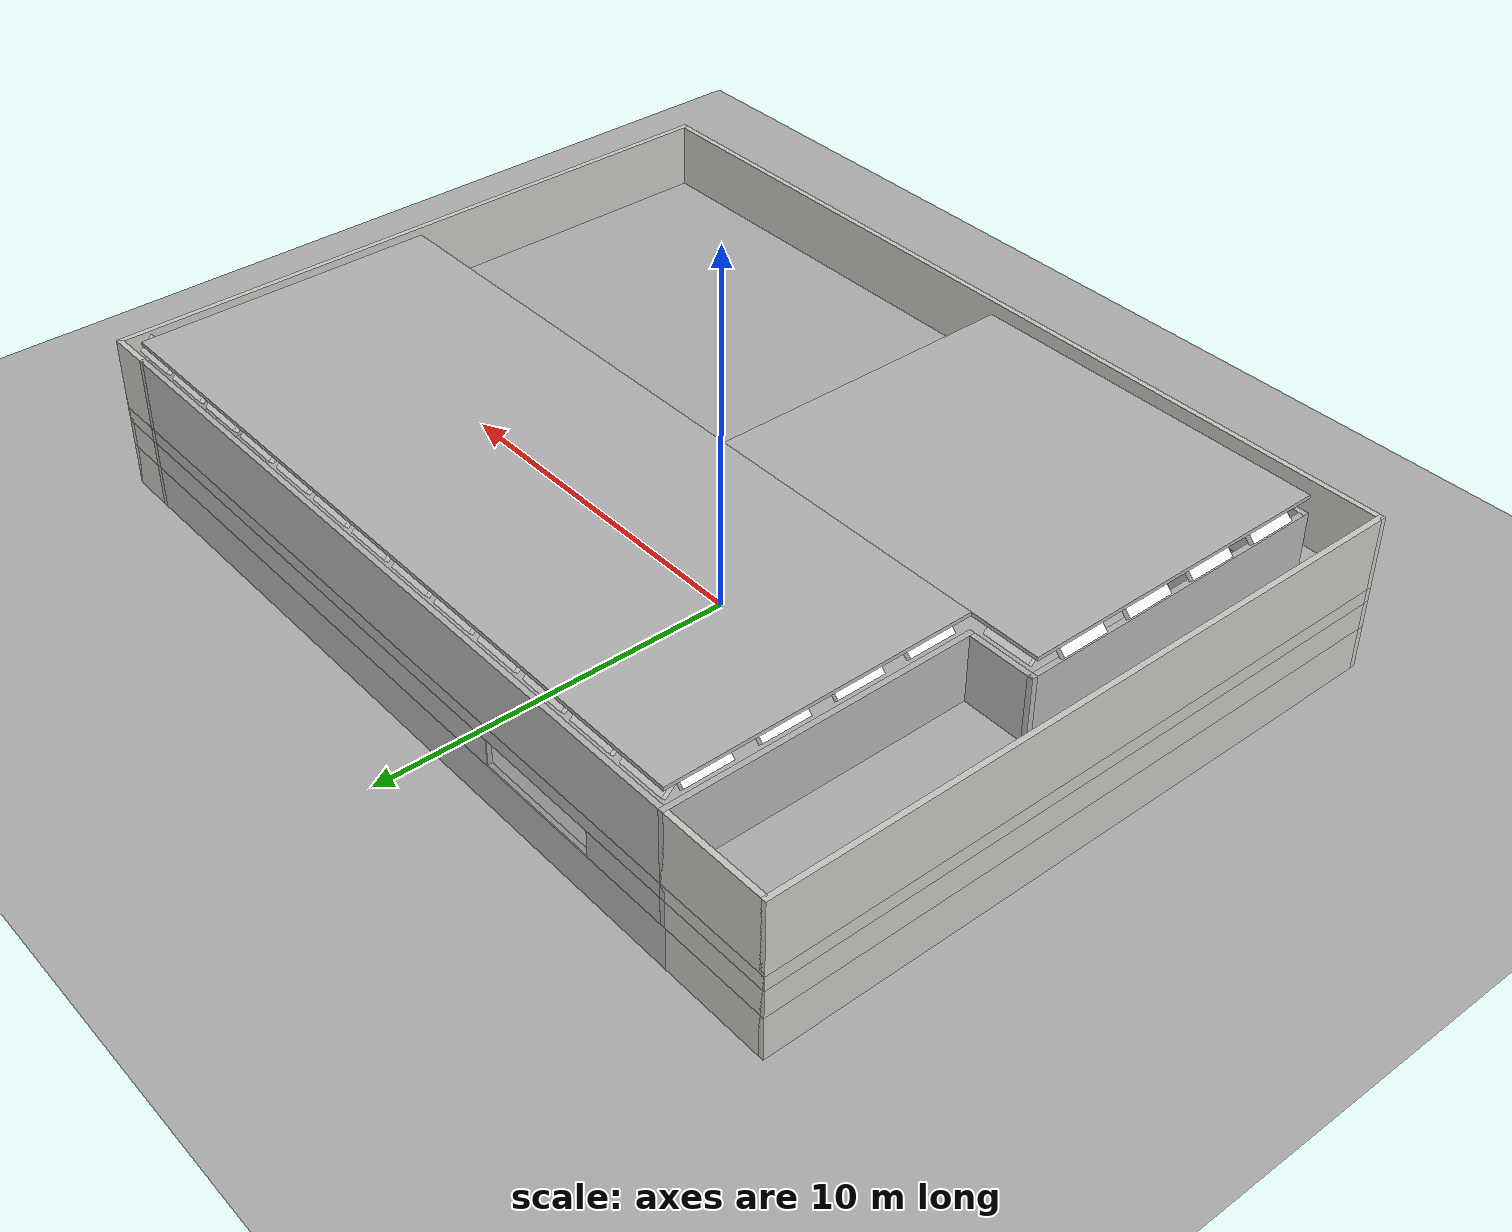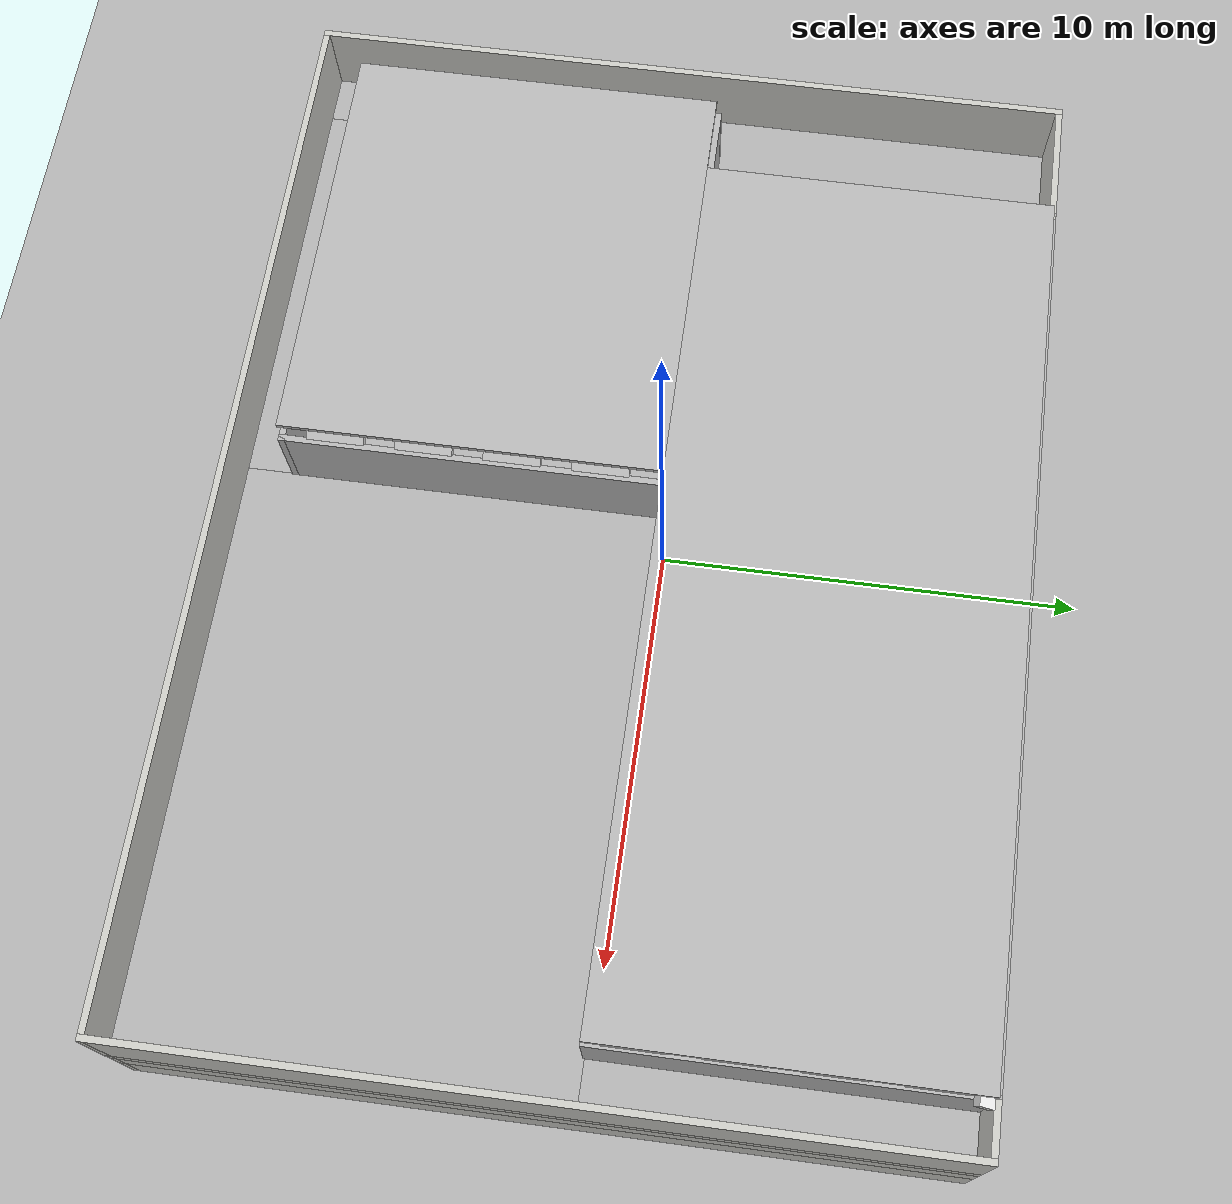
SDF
<sdf version="1.6">
 <world name="default">
  <model name="ground_plane">
   <static>1</static>
   <link name="link">
    <collision name="collision">
     <geometry><plane><normal>0 0 1</normal><size>30 25</size></plane></geometry>
     <surface><friction><ode><mu>100</mu><mu2>50</mu2></ode></friction></surface>
    </collision>
    <visual name="visual">
     <cast_shadows>0</cast_shadows>
     <geometry><plane><normal>0 0 1</normal><size>30 25</size></plane></geometry>
     <material>
      <script>
       <uri>model://ground/materials/scripts</uri>
       <uri>model://ground/materials/textures</uri>
       <name>ground</name>
      </script>
      <ambient>0.6 0.6 0.6 1</ambient>
      <diffuse>0.7 0.7 0.7 1</diffuse>
      <specular>0.2 0.2 0.2 1</specular>
     </material>
    </visual>
   </link>
  </model>
  <gravity>0 0 -9.8</gravity>
  <magnetic_field>6e-06 2.3e-05 -4.2e-05</magnetic_field>
  <atmosphere type="adiabatic"/>
  <physics name="default_physics" default="0" type="ode">
   <max_step_size>0.001</max_step_size>
   <real_time_factor>1</real_time_factor>
   <real_time_update_rate>0</real_time_update_rate>
   <ode>
    <solver>
     <thread_position_correction>1</thread_position_correction>
     <island_threads>500</island_threads>
    </solver>
   </ode>
  </physics>
  <scene><ambient>0.4 0.4 0.4 1</ambient><background>0.7 0.7 0.7 1</background><shadows>0</shadows></scene>
  <spherical_coordinates>
   <surface_model>EARTH_WGS84</surface_model>
   <latitude_deg>0</latitude_deg>
   <longitude_deg>0</longitude_deg>
   <elevation>0</elevation>
   <heading_deg>0</heading_deg>
  </spherical_coordinates>
  <model name="FAV5">
   <pose>1.15 -0.8 0 0 -0 0</pose>
   <static>true</static>
   <link name="logo_1">
    <pose>11.05 4.9 1 0 -0 0</pose>
    <visual name="visual">
     <pose>0 0 1.5 0 -0 0</pose>
     <geometry><box><size>0.1 2 2</size></box></geometry>
     <material>
      <lighting>1</lighting>
      <script>
       <uri>model://logo1/materials/scripts</uri>
       <uri>model://logo1/materials/textures</uri>
       <name>logo1/logo</name>
      </script>
     </material>
    </visual>
    <collision name="collision">
     <pose>0 0 1 0 -0 0</pose>
     <geometry><box><size>0.1 2 2</size></box></geometry>
     <surface>
      <friction>
       <ode><mu>1</mu><mu2>1</mu2><fdir1>0 0 0</fdir1><slip1>0</slip1><slip2>0</slip2></ode>
       <torsional>
        <coefficient>1</coefficient>
        <patch_radius>0</patch_radius>
        <surface_radius>0</surface_radius>
        <use_patch_radius>1</use_patch_radius>
        <ode><slip>0</slip></ode>
       </torsional>
      </friction>
      <bounce><restitution_coefficient>0</restitution_coefficient><threshold>1e+06</threshold></bounce>
      <contact>
       <collide_without_contact>0</collide_without_contact>
       <collide_without_contact_bitmask>1</collide_without_contact_bitmask>
       <collide_bitmask>1</collide_bitmask>
       <ode>
        <soft_cfm>0</soft_cfm>
        <soft_erp>0.2</soft_erp>
        <kp>1e+13</kp>
        <kd>1</kd>
        <max_vel>0.01</max_vel>
        <min_depth>0</min_depth>
       </ode>
       <bullet>
        <split_impulse>1</split_impulse>
        <split_impulse_penetration_threshold>-0.01</split_impulse_penetration_threshold>
        <soft_cfm>0</soft_cfm>
        <soft_erp>0.2</soft_erp>
        <kp>1e+13</kp>
        <kd>1</kd>
       </bullet>
      </contact>
     </surface>
    </collision>
   </link>
   <static>true</static>
   <link name="logo_1_clone">
    <pose>-6.1 -7.8 1 0 -0 0</pose>
    <visual name="visual">
     <pose>0 0 1.5 0 -0 1.57</pose>
     <geometry><box><size>0.1 2 2</size></box></geometry>
     <material>
      <lighting>1</lighting>
      <script>
       <uri>model://logo1/materials/scripts</uri>
       <uri>model://logo1/materials/textures</uri>
       <name>logo1/logo</name>
      </script>
     </material>
    </visual>
    <collision name="collision">
     <pose>0 0 1.5 0 -0 1.57</pose>
     <geometry><box><size>0.1 2 2</size></box></geometry>
     <surface>
      <friction>
       <ode><mu>1</mu><mu2>1</mu2><fdir1>0 0 0</fdir1><slip1>0</slip1><slip2>0</slip2></ode>
       <torsional>
        <coefficient>1</coefficient>
        <patch_radius>0</patch_radius>
        <surface_radius>0</surface_radius>
        <use_patch_radius>1</use_patch_radius>
        <ode><slip>0</slip></ode>
       </torsional>
      </friction>
      <bounce><restitution_coefficient>0</restitution_coefficient><threshold>1e+06</threshold></bounce>
      <contact>
       <collide_without_contact>0</collide_without_contact>
       <collide_without_contact_bitmask>1</collide_without_contact_bitmask>
       <collide_bitmask>1</collide_bitmask>
       <ode>
        <soft_cfm>0</soft_cfm>
        <soft_erp>0.2</soft_erp>
        <kp>1e+13</kp>
        <kd>1</kd>
        <max_vel>0.01</max_vel>
        <min_depth>0</min_depth>
       </ode>
       <bullet>
        <split_impulse>1</split_impulse>
        <split_impulse_penetration_threshold>-0.01</split_impulse_penetration_threshold>
        <soft_cfm>0</soft_cfm>
        <soft_erp>0.2</soft_erp>
        <kp>1e+13</kp>
        <kd>1</kd>
       </bullet>
      </contact>
     </surface>
    </collision>
   </link>
   <link name="logo_2">
    <pose>3.65 8.9 1 0 -0 0</pose>
    <visual name="visual">
     <pose>0 0 1.5 0 -0 0</pose>
     <geometry><box><size>4.875 0.1 1.5</size></box></geometry>
     <material>
      <lighting>1</lighting>
      <script>
       <uri>model://logo2/materials/scripts</uri>
       <uri>model://logo2/materials/textures</uri>
       <name>logo2/logo</name>
      </script>
     </material>
    </visual>
    <collision name="collision">
     <pose>0 0 1.5 0 -0 0</pose>
     <geometry><box><size>4.875 0.1 1.5</size></box></geometry>
     <surface>
      <friction>
       <ode><mu>1</mu><mu2>1</mu2><fdir1>0 0 0</fdir1><slip1>0</slip1><slip2>0</slip2></ode>
       <torsional>
        <coefficient>1</coefficient>
        <patch_radius>0</patch_radius>
        <surface_radius>0</surface_radius>
        <use_patch_radius>1</use_patch_radius>
        <ode><slip>0</slip></ode>
       </torsional>
      </friction>
      <bounce><restitution_coefficient>0</restitution_coefficient><threshold>1e+06</threshold></bounce>
      <contact>
       <collide_without_contact>0</collide_without_contact>
       <collide_without_contact_bitmask>1</collide_without_contact_bitmask>
       <collide_bitmask>1</collide_bitmask>
       <ode>
        <soft_cfm>0</soft_cfm>
        <soft_erp>0.2</soft_erp>
        <kp>1e+13</kp>
        <kd>1</kd>
        <max_vel>0.01</max_vel>
        <min_depth>0</min_depth>
       </ode>
       <bullet>
        <split_impulse>1</split_impulse>
        <split_impulse_penetration_threshold>-0.01</split_impulse_penetration_threshold>
        <soft_cfm>0</soft_cfm>
        <soft_erp>0.2</soft_erp>
        <kp>1e+13</kp>
        <kd>1</kd>
       </bullet>
      </contact>
     </surface>
    </collision>
   </link>
   <link name="Wall_138">
    <collision name="Wall_138_Collision">
     <geometry><box><size>12.45 0.15 1.2</size></box></geometry>
     <pose>0 0 0.6 0 -0 0</pose>
    </collision>
    <visual name="Wall_138_Visual">
     <pose>0 0 0.6 0 -0 0</pose>
     <geometry><box><size>12.45 0.15 1.2</size></box></geometry>
     <material>
      <script>
       <uri>model://FAV5/materials/scripts</uri>
       <uri>model://FAV5/materials/textures</uri>
       <name>FAV5/FAV5</name>
      </script>
     </material>
     <meta><layer>0</layer></meta>
    </visual>
    <pose>4.95 0.85 0 0 -0 0</pose>
   </link>
   <link name="Wall_140">
    <collision name="Wall_140_Collision">
     <geometry><box><size>8.35 0.15 1.2</size></box></geometry>
     <pose>0 0 0.6 0 -0 0</pose>
    </collision>
    <visual name="Wall_140_Visual">
     <pose>0 0 0.6 0 -0 0</pose>
     <geometry><box><size>8.35 0.15 1.2</size></box></geometry>
     <material>
      <script>
       <uri>model://FAV5/materials/scripts</uri>
       <uri>model://FAV5/materials/textures</uri>
       <name>FAV5/FAV5</name>
      </script>
     </material>
     <meta><layer>0</layer></meta>
    </visual>
    <pose>11.1 4.95 0 0 -0 1.5708</pose>
   </link>
   <link name="Wall_141">
    <collision name="Wall_141_Collision">
     <geometry><box><size>20.55 0.15 1.2</size></box></geometry>
     <pose>0 0 0.6 0 -0 0</pose>
    </collision>
    <visual name="Wall_141_Visual">
     <pose>0 0 0.6 0 -0 0</pose>
     <geometry><box><size>20.55 0.15 1.2</size></box></geometry>
     <material>
      <script>
       <uri>model://FAV5/materials/scripts</uri>
       <uri>model://FAV5/materials/textures</uri>
       <name>FAV5/FAV5</name>
      </script>
     </material>
     <meta><layer>0</layer></meta>
    </visual>
    <pose>0.9 9.05 0 0 -0 3.14159</pose>
   </link>
   <link name="Wall_142">
    <collision name="Wall_142_Collision">
     <geometry><box><size>8.35 0.15 1.2</size></box></geometry>
     <pose>0 0 0.6 0 -0 0</pose>
    </collision>
    <visual name="Wall_142_Visual">
     <pose>0 0 0.6 0 -0 0</pose>
     <geometry><box><size>8.35 0.15 1.2</size></box></geometry>
     <material>
      <script>
       <uri>model://FAV5/materials/scripts</uri>
       <uri>model://FAV5/materials/textures</uri>
       <name>FAV5/FAV5</name>
      </script>
     </material>
     <meta><layer>0</layer></meta>
    </visual>
    <pose>-9.3 4.95 0 0 -0 -1.5708</pose>
   </link>
   <link name="Wall_143">
    <collision name="Wall_143_Collision">
     <geometry><box><size>1.95 0.15 1.2</size></box></geometry>
     <pose>0 0 0.6 0 -0 0</pose>
    </collision>
    <visual name="Wall_143_Visual">
     <pose>0 0 0.6 0 -0 0</pose>
     <geometry><box><size>1.95 0.15 1.2</size></box></geometry>
     <material>
      <script>
       <uri>model://FAV5/materials/scripts</uri>
       <uri>model://FAV5/materials/textures</uri>
       <name>FAV5/FAV5</name>
      </script>
     </material>
     <meta><layer>0</layer></meta>
    </visual>
    <pose>-10.2 0.85 0 0 -0 3.14159</pose>
   </link>
   <link name="Wall_144">
    <collision name="Wall_144_Collision">
     <geometry><box><size>8.85057 0.15 1.2</size></box></geometry>
     <pose>0 0 0.6 0 -0 0</pose>
    </collision>
    <visual name="Wall_144_Visual">
     <pose>0 0 0.6 0 -0 0</pose>
     <geometry><box><size>8.85057 0.15 1.2</size></box></geometry>
     <material>
      <script>
       <uri>model://FAV5/materials/scripts</uri>
       <uri>model://FAV5/materials/textures</uri>
       <name>FAV5/FAV5</name>
      </script>
     </material>
     <meta><layer>0</layer></meta>
    </visual>
    <pose>-11.1 -3.5 0 0 -0 -1.5708</pose>
   </link>
   <link name="Wall_145">
    <collision name="Wall_145_Collision">
     <geometry><box><size>10.05 0.15 1.2</size></box></geometry>
     <pose>0 0 0.6 0 -0 0</pose>
    </collision>
    <visual name="Wall_145_Visual">
     <pose>0 0 0.6 0 -0 0</pose>
     <geometry><box><size>10.05 0.15 1.2</size></box></geometry>
     <material>
      <script>
       <uri>model://FAV5/materials/scripts</uri>
       <uri>model://FAV5/materials/textures</uri>
       <name>FAV5/FAV5</name>
      </script>
     </material>
     <meta><layer>0</layer></meta>
    </visual>
    <pose>-6.15 -7.85 0 0 -0 0</pose>
   </link>
   <link name="Wall_146">
    <collision name="Wall_146_Collision">
     <geometry><box><size>8.85 0.15 1.2</size></box></geometry>
     <pose>0 0 0.6 0 -0 0</pose>
    </collision>
    <visual name="Wall_146_Visual">
     <pose>0 0 0.6 0 -0 0</pose>
     <geometry><box><size>8.85 0.15 1.2</size></box></geometry>
     <material>
      <script>
       <uri>model://FAV5/materials/scripts</uri>
       <uri>model://FAV5/materials/textures</uri>
       <name>FAV5/FAV5</name>
      </script>
     </material>
     <meta><layer>0</layer></meta>
    </visual>
    <pose>-1.2 -3.5 0 0 -0 1.5708</pose>
   </link>
   <link name="Wall_148">
    <collision name="Wall_148_Collision">
     <geometry><box><size>1.35 0.15 1.2</size></box></geometry>
     <pose>0 0 0.6 0 -0 0</pose>
    </collision>
    <visual name="Wall_148_Visual">
     <pose>0 0 0.6 0 -0 0</pose>
     <geometry><box><size>1.35 0.15 1.2</size></box></geometry>
     <material>
      <script><uri>file://media/materials/scripts/gazebo.material</uri><name>Gazebo/CeilingTiled</name></script>
      <ambient>1 1 1 1</ambient>
     </material>
     <meta><layer>0</layer></meta>
    </visual>
    <pose>11.7 9.05 0 0 -0 0</pose>
   </link>
   <link name="Wall_149">
    <collision name="Wall_149_Collision">
     <geometry><box><size>18.25 0.15 1.2</size></box></geometry>
     <pose>0 0 0.6 0 -0 0</pose>
    </collision>
    <visual name="Wall_149_Visual">
     <pose>0 0 0.6 0 -0 0</pose>
     <geometry><box><size>18.25 0.15 1.2</size></box></geometry>
     <material>
      <script><uri>file://media/materials/scripts/gazebo.material</uri><name>Gazebo/CeilingTiled</name></script>
      <ambient>1 1 1 1</ambient>
     </material>
     <meta><layer>0</layer></meta>
    </visual>
    <pose>12.3 0 0 0 -0 -1.5708</pose>
   </link>
   <link name="Wall_151">
    <collision name="Wall_151_Collision">
     <geometry><box><size>18.25 0.15 1.2</size></box></geometry>
     <pose>0 0 0.6 0 -0 0</pose>
    </collision>
    <visual name="Wall_151_Visual">
     <pose>0 0 0.6 0 -0 0</pose>
     <geometry><box><size>18.25 0.15 1.2</size></box></geometry>
     <material>
      <script><uri>file://media/materials/scripts/gazebo.material</uri><name>Gazebo/CeilingTiled</name></script>
      <ambient>1 1 1 1</ambient>
     </material>
     <meta><layer>0</layer></meta>
    </visual>
    <pose>-12.3 0 0 0 -0 1.5708</pose>
   </link>
   <link name="Wall_152">
    <collision name="Wall_152_Collision">
     <geometry><box><size>3.15 0.15 1.2</size></box></geometry>
     <pose>0 0 0.6 0 -0 0</pose>
    </collision>
    <visual name="Wall_152_Visual">
     <pose>0 0 0.6 0 -0 0</pose>
     <geometry><box><size>3.15 0.15 1.2</size></box></geometry>
     <material>
      <script><uri>file://media/materials/scripts/gazebo.material</uri><name>Gazebo/CeilingTiled</name></script>
      <ambient>1 1 1 1</ambient>
     </material>
     <meta><layer>0</layer></meta>
    </visual>
    <pose>-10.8 9.05 0 0 -0 0</pose>
   </link>
   <link name="Wall_154">
    <collision name="Wall_154_Collision">
     <geometry><box><size>24.75 0.15 1.2</size></box></geometry>
     <pose>0 0 0.6 0 -0 0</pose>
    </collision>
    <visual name="Wall_154_Visual">
     <pose>0 0 0.6 0 -0 0</pose>
     <geometry><box><size>24.75 0.15 1.2</size></box></geometry>
     <material>
      <script><uri>file://media/materials/scripts/gazebo.material</uri><name>Gazebo/CeilingTiled</name></script>
      <ambient>1 1 1 1</ambient>
     </material>
     <meta><layer>0</layer></meta>
    </visual>
    <pose>0 -9.05 0 0 -0 3.14159</pose>
   </link>
   <link name="Wall_157">
    <collision name="Wall_157_Collision">
     <geometry><box><size>8.35 0.15 0.75</size></box></geometry>
     <pose>0 0 0.375 0 -0 0</pose>
    </collision>
    <visual name="Wall_157_Visual">
     <pose>0 0 0.375 0 -0 0</pose>
     <geometry><box><size>8.35 0.15 0.75</size></box></geometry>
     <material>
      <script>
       <uri>model://FAV5/materials/scripts</uri>
       <uri>model://FAV5/materials/textures</uri>
       <name>FAV5/FAV5</name>
      </script>
     </material>
     <meta><layer>1</layer></meta>
    </visual>
    <pose>11.1 4.95 1.2 0 -0 1.5708</pose>
   </link>
   <link name="Wall_161">
    <collision name="Wall_161_Collision">
     <geometry><box><size>8.85 0.15 0.75</size></box></geometry>
     <pose>0 0 0.375 0 -0 0</pose>
    </collision>
    <visual name="Wall_161_Visual">
     <pose>0 0 0.375 0 -0 0</pose>
     <geometry><box><size>8.85 0.15 0.75</size></box></geometry>
     <material>
      <script>
       <uri>model://FAV5/materials/scripts</uri>
       <uri>model://FAV5/materials/textures</uri>
       <name>FAV5/FAV5</name>
      </script>
     </material>
     <meta><layer>1</layer></meta>
    </visual>
    <pose>-11.1 -3.5 1.2 0 -0 -1.5708</pose>
   </link>
   <link name="Wall_162">
    <collision name="Wall_162_Collision">
     <geometry><box><size>10.05 0.15 0.75</size></box></geometry>
     <pose>0 0 0.375 0 -0 0</pose>
    </collision>
    <visual name="Wall_162_Visual">
     <pose>0 0 0.375 0 -0 0</pose>
     <geometry><box><size>10.05 0.15 0.75</size></box></geometry>
     <material>
      <script>
       <uri>model://FAV5/materials/scripts</uri>
       <uri>model://FAV5/materials/textures</uri>
       <name>FAV5/FAV5</name>
      </script>
     </material>
     <meta><layer>1</layer></meta>
    </visual>
    <pose>-6.15 -7.85 1.2 0 -0 0</pose>
   </link>
   <link name="Wall_164">
    <collision name="Wall_164_Collision">
     <geometry><box><size>1.35 0.15 0.75</size></box></geometry>
     <pose>0 0 0.375 0 -0 0</pose>
    </collision>
    <visual name="Wall_164_Visual">
     <pose>0 0 0.375 0 -0 0</pose>
     <geometry><box><size>1.35 0.15 0.75</size></box></geometry>
     <material>
      <script><uri>file://media/materials/scripts/gazebo.material</uri><name>Gazebo/CeilingTiled</name></script>
      <ambient>1 1 1 1</ambient>
     </material>
     <meta><layer>1</layer></meta>
    </visual>
    <pose>11.7 9.05 1.2 0 -0 0</pose>
   </link>
   <link name="Wall_165">
    <collision name="Wall_165_Collision">
     <geometry><box><size>18.25 0.15 0.75</size></box></geometry>
     <pose>0 0 0.375 0 -0 0</pose>
    </collision>
    <visual name="Wall_165_Visual">
     <pose>0 0 0.375 0 -0 0</pose>
     <geometry><box><size>18.25 0.15 0.75</size></box></geometry>
     <material>
      <script><uri>file://media/materials/scripts/gazebo.material</uri><name>Gazebo/CeilingTiled</name></script>
      <ambient>1 1 1 1</ambient>
     </material>
     <meta><layer>1</layer></meta>
    </visual>
    <pose>12.3 0 1.2 0 -0 -1.5708</pose>
   </link>
   <link name="Wall_166">
    <collision name="Wall_166_Collision">
     <geometry><box><size>18.25 0.15 0.75</size></box></geometry>
     <pose>0 0 0.375 0 -0 0</pose>
    </collision>
    <visual name="Wall_166_Visual">
     <pose>0 0 0.375 0 -0 0</pose>
     <geometry><box><size>18.25 0.15 0.75</size></box></geometry>
     <material>
      <script><uri>file://media/materials/scripts/gazebo.material</uri><name>Gazebo/CeilingTiled</name></script>
      <ambient>1 1 1 1</ambient>
     </material>
     <meta><layer>1</layer></meta>
    </visual>
    <pose>-12.3 0 1.2 0 -0 1.5708</pose>
   </link>
   <link name="Wall_167">
    <collision name="Wall_167_Collision">
     <geometry><box><size>3.15 0.15 0.75</size></box></geometry>
     <pose>0 0 0.375 0 -0 0</pose>
    </collision>
    <visual name="Wall_167_Visual">
     <pose>0 0 0.375 0 -0 0</pose>
     <geometry><box><size>3.15 0.15 0.75</size></box></geometry>
     <material>
      <script><uri>file://media/materials/scripts/gazebo.material</uri><name>Gazebo/CeilingTiled</name></script>
      <ambient>1 1 1 1</ambient>
     </material>
     <meta><layer>1</layer></meta>
    </visual>
    <pose>-10.8 9.05 1.2 0 -0 0</pose>
   </link>
   <link name="Wall_168">
    <collision name="Wall_168_Collision">
     <geometry><box><size>24.75 0.15 0.75</size></box></geometry>
     <pose>0 0 0.375 0 -0 0</pose>
    </collision>
    <visual name="Wall_168_Visual">
     <pose>0 0 0.375 0 -0 0</pose>
     <geometry><box><size>24.75 0.15 0.75</size></box></geometry>
     <material>
      <script><uri>file://media/materials/scripts/gazebo.material</uri><name>Gazebo/CeilingTiled</name></script>
      <ambient>1 1 1 1</ambient>
     </material>
     <meta><layer>1</layer></meta>
    </visual>
    <pose>0 -9.05 1.2 0 -0 3.14159</pose>
   </link>
   <link name="Wall_169">
    <visual name="Wall_169_Visual">
     <pose>0 0 0.375 0 -0 0</pose>
     <geometry><box><size>6.45 0.1 0.75</size></box></geometry>
     <material name="my_material">
      <ambient>0.5 0.5 0.5 1</ambient>
      <diffuse>0.8 0.8 0.8 0.5</diffuse>
      <transparent>true</transparent>
      <opacity>0.2</opacity>
     </material>
     <meta><layer>1</layer></meta>
    </visual>
    <pose>-9.3 4.125 1.2 0 -0 1.5708</pose>
   </link>
   <gazebo reference="Wall_169">
    <material>Gazebo/Glass</material>
    <sensor name="laser_transparency">
     <transmissivity>0.85</transmissivity>
     <reflectivity>0.15</reflectivity>
    </sensor>
   </gazebo>
   <link name="Wall_170">
    <collision name="Wall_170_Collision">
     <geometry><box><size>1.9 0.15 0.75</size></box></geometry>
     <pose>0 0 0.375 0 -0 0</pose>
    </collision>
    <visual name="Wall_170_Visual">
     <pose>0 0 0.375 0 -0 0</pose>
     <geometry><box><size>1.9 0.15 0.75</size></box></geometry>
     <material>
      <script>
       <uri>model://FAV5/materials/scripts</uri>
       <uri>model://FAV5/materials/textures</uri>
       <name>FAV5/FAV5</name>
      </script>
     </material>
     <meta><layer>1</layer></meta>
    </visual>
    <pose>-9.3 8.175 1.2 0 -0 1.5708</pose>
   </link>
   <link name="Wall_172">
    <collision name="Wall_172_Collision">
     <geometry><box><size>0.25 0.15 0.75</size></box></geometry>
     <pose>0 0 0.375 0 -0 0</pose>
    </collision>
    <visual name="Wall_172_Visual">
     <pose>0 0 0.375 0 -0 0</pose>
     <geometry><box><size>0.25 0.15 0.75</size></box></geometry>
     <material>
      <script>
       <uri>model://FAV5/materials/scripts</uri>
       <uri>model://FAV5/materials/textures</uri>
       <name>FAV5/FAV5</name>
      </script>
     </material>
     <meta><layer>1</layer></meta>
    </visual>
    <pose>-9.3 0.9 1.2 0 -0 -1.5708</pose>
   </link>
   <link name="Wall_175">
    <collision name="Wall_175_Collision">
     <geometry><box><size>0.25 0.15 0.75</size></box></geometry>
     <pose>0 0 0.375 0 -0 0</pose>
    </collision>
    <visual name="Wall_175_Visual">
     <pose>0 0 0.375 0 -0 0</pose>
     <geometry><box><size>0.25 0.15 0.75</size></box></geometry>
     <material>
      <script>
       <uri>model://FAV5/materials/scripts</uri>
       <uri>model://FAV5/materials/textures</uri>
       <name>FAV5/FAV5</name>
      </script>
     </material>
     <meta><layer>1</layer></meta>
    </visual>
    <pose>-9.35 0.85 1.2 0 -0 0</pose>
   </link>
   <link name="Wall_177">
    <visual name="Wall_177_Visual">
     <pose>0 0 0.375 0 -0 0</pose>
     <geometry><box><size>1.8 0.1 0.75</size></box></geometry>
     <material name="my_material">
      <ambient>0.5 0.5 0.5 1</ambient>
      <diffuse>0.8 0.8 0.8 0.5</diffuse>
      <transparent>true</transparent>
      <opacity>0.2</opacity>
     </material>
     <meta><layer>1</layer></meta>
    </visual>
    <pose>-10.25 0.85 1.2 0 -0 0</pose>
   </link>
   <gazebo reference="Wall_177">
    <material>Gazebo/Glass</material>
    <sensor name="laser_transparency">
     <transmissivity>0.85</transmissivity>
     <reflectivity>0.15</reflectivity>
    </sensor>
   </gazebo>
   <link name="Wall_179">
    <collision name="Wall_179_Collision">
     <geometry><box><size>0.25 0.15 0.75</size></box></geometry>
     <pose>0 0 0.375 0 -0 0</pose>
    </collision>
    <visual name="Wall_179_Visual">
     <pose>0 0 0.375 0 -0 0</pose>
     <geometry><box><size>0.25 0.15 0.75</size></box></geometry>
     <material>
      <script>
       <uri>model://FAV5/materials/scripts</uri>
       <uri>model://FAV5/materials/textures</uri>
       <name>FAV5/FAV5</name>
      </script>
     </material>
     <meta><layer>1</layer></meta>
    </visual>
    <pose>-1.2 0.8 1.2 0 -0 -1.5708</pose>
   </link>
   <link name="Wall_181">
    <visual name="Wall_181_Visual">
     <pose>0 0 0.375 0 -0 0</pose>
     <geometry><box><size>8.7 0.1 0.75</size></box></geometry>
     <material name="my_material">
      <ambient>0.5 0.5 0.5 1</ambient>
      <diffuse>0.8 0.8 0.8 0.5</diffuse>
      <transparent>true</transparent>
      <opacity>0.2</opacity>
     </material>
     <meta><layer>1</layer></meta>
    </visual>
    <pose>-1.2 -3.55 1.2 0 -0 1.5708</pose>
   </link>
   <gazebo reference="Wall_181">
    <material>Gazebo/Glass</material>
    <sensor name="laser_transparency">
     <transmissivity>0.85</transmissivity>
     <reflectivity>0.15</reflectivity>
    </sensor>
   </gazebo>
   <link name="Wall_185">
    <collision name="Wall_185_Collision">
     <geometry><box><size>0.25 0.15 0.75</size></box></geometry>
     <pose>0 0 0.375 0 -0 0</pose>
    </collision>
    <visual name="Wall_185_Visual">
     <pose>0 0 0.375 0 -0 0</pose>
     <geometry><box><size>0.25 0.15 0.75</size></box></geometry>
     <material>
      <script>
       <uri>model://FAV5/materials/scripts</uri>
       <uri>model://FAV5/materials/textures</uri>
       <name>FAV5/FAV5</name>
      </script>
     </material>
     <meta><layer>1</layer></meta>
    </visual>
    <pose>-1.15 0.85 1.2 0 -0 3.14159</pose>
   </link>
   <link name="Wall_187">
    <visual name="Wall_187_Visual">
     <pose>0 0 0.375 0 -0 0</pose>
     <geometry><box><size>12.3 0.1 0.75</size></box></geometry>
     <material name="my_material">
      <ambient>0.5 0.5 0.5 1</ambient>
      <diffuse>0.8 0.8 0.8 0.5</diffuse>
      <transparent>true</transparent>
      <opacity>0.2</opacity>
     </material>
     <meta><layer>1</layer></meta>
    </visual>
    <pose>5 0.85 1.2 0 -0 0</pose>
   </link>
   <gazebo reference="Wall_187">
    <material>Gazebo/Glass</material>
    <sensor name="laser_transparency">
     <transmissivity>0.85</transmissivity>
     <reflectivity>0.15</reflectivity>
    </sensor>
   </gazebo>
   <link name="Wall_189">
    <collision name="Wall_189_Collision">
     <geometry><box><size>2.55 0.15 0.75</size></box></geometry>
     <pose>0 0 0.375 0 -0 0</pose>
    </collision>
    <visual name="Wall_189_Visual">
     <pose>0 0 0.375 0 -0 0</pose>
     <geometry><box><size>2.55 0.15 0.75</size></box></geometry>
     <material>
      <script>
       <uri>model://FAV5/materials/scripts</uri>
       <uri>model://FAV5/materials/textures</uri>
       <name>FAV5/FAV5</name>
      </script>
     </material>
     <meta><layer>1</layer></meta>
    </visual>
    <pose>-8.1 9.05 1.2 0 -0 0</pose>
   </link>
   <link name="Wall_190">
    <visual name="Wall_190_Visual">
     <pose>0 0 0.375 0 -0 0</pose>
     <geometry><box><size>3.8 0.1 0.75</size></box></geometry>
     <material name="my_material">
      <ambient>0.5 0.5 0.5 1</ambient>
      <diffuse>0.8 0.8 0.8 0.5</diffuse>
      <transparent>true</transparent>
      <opacity>0.2</opacity>
     </material>
     <meta><layer>1</layer></meta>
    </visual>
    <pose>-5.05 9.05 1.2 0 -0 0</pose>
   </link>
   <gazebo reference="Wall_190">
    <material>Gazebo/Glass</material>
    <sensor name="laser_transparency">
     <transmissivity>0.85</transmissivity>
     <reflectivity>0.15</reflectivity>
    </sensor>
   </gazebo>
   <link name="Wall_191">
    <collision name="Wall_191_Collision">
     <geometry><box><size>14.35 0.15 0.75</size></box></geometry>
     <pose>0 0 0.375 0 -0 0</pose>
    </collision>
    <visual name="Wall_191_Visual">
     <pose>0 0 0.375 0 -0 0</pose>
     <geometry><box><size>14.35 0.15 0.75</size></box></geometry>
     <material>
      <script>
       <uri>model://FAV5/materials/scripts</uri>
       <uri>model://FAV5/materials/textures</uri>
       <name>FAV5/FAV5</name>
      </script>
     </material>
     <meta><layer>1</layer></meta>
    </visual>
    <pose>3.9 9.05 1.2 0 -0 0</pose>
   </link>
   <link name="Wall_193">
    <collision name="Wall_193_Collision">
     <geometry><box><size>8.35 0.15 0.4</size></box></geometry>
     <pose>0 0 0.2 0 -0 0</pose>
    </collision>
    <visual name="Wall_193_Visual">
     <pose>0 0 0.2 0 -0 0</pose>
     <geometry><box><size>8.35 0.15 0.4</size></box></geometry>
     <material>
      <script>
       <uri>model://FAV5/materials/scripts</uri>
       <uri>model://FAV5/materials/textures</uri>
       <name>FAV5/FAV5</name>
      </script>
     </material>
     <meta><layer>2</layer></meta>
    </visual>
    <pose>11.1 4.95 1.95 0 -0 1.5708</pose>
   </link>
   <link name="Wall_194">
    <collision name="Wall_194_Collision">
     <geometry><box><size>8.85 0.15 0.4</size></box></geometry>
     <pose>0 0 0.2 0 -0 0</pose>
    </collision>
    <visual name="Wall_194_Visual">
     <pose>0 0 0.2 0 -0 0</pose>
     <geometry><box><size>8.85 0.15 0.4</size></box></geometry>
     <material>
      <script>
       <uri>model://FAV5/materials/scripts</uri>
       <uri>model://FAV5/materials/textures</uri>
       <name>FAV5/FAV5</name>
      </script>
     </material>
     <meta><layer>2</layer></meta>
    </visual>
    <pose>-11.1 -3.5 1.95 0 -0 -1.5708</pose>
   </link>
   <link name="Wall_195">
    <collision name="Wall_195_Collision">
     <geometry><box><size>10.05 0.15 0.4</size></box></geometry>
     <pose>0 0 0.2 0 -0 0</pose>
    </collision>
    <visual name="Wall_195_Visual">
     <pose>0 0 0.2 0 -0 0</pose>
     <geometry><box><size>10.05 0.15 0.4</size></box></geometry>
     <material>
      <script>
       <uri>model://FAV5/materials/scripts</uri>
       <uri>model://FAV5/materials/textures</uri>
       <name>FAV5/FAV5</name>
      </script>
     </material>
     <meta><layer>2</layer></meta>
    </visual>
    <pose>-6.15 -7.85 1.95 0 -0 0</pose>
   </link>
   <link name="Wall_196">
    <collision name="Wall_196_Collision">
     <geometry><box><size>1.35 0.15 0.4</size></box></geometry>
     <pose>0 0 0.2 0 -0 0</pose>
    </collision>
    <visual name="Wall_196_Visual">
     <pose>0 0 0.2 0 -0 0</pose>
     <geometry><box><size>1.35 0.15 0.4</size></box></geometry>
     <material>
      <script><uri>file://media/materials/scripts/gazebo.material</uri><name>Gazebo/CeilingTiled</name></script>
      <ambient>1 1 1 1</ambient>
     </material>
     <meta><layer>2</layer></meta>
    </visual>
    <pose>11.7 9.05 1.95 0 -0 0</pose>
   </link>
   <link name="Wall_197">
    <collision name="Wall_197_Collision">
     <geometry><box><size>18.25 0.15 0.4</size></box></geometry>
     <pose>0 0 0.2 0 -0 0</pose>
    </collision>
    <visual name="Wall_197_Visual">
     <pose>0 0 0.2 0 -0 0</pose>
     <geometry><box><size>18.25 0.15 0.4</size></box></geometry>
     <material>
      <script><uri>file://media/materials/scripts/gazebo.material</uri><name>Gazebo/CeilingTiled</name></script>
      <ambient>1 1 1 1</ambient>
     </material>
     <meta><layer>2</layer></meta>
    </visual>
    <pose>12.3 0 1.95 0 -0 -1.5708</pose>
   </link>
   <link name="Wall_198">
    <collision name="Wall_198_Collision">
     <geometry><box><size>18.25 0.15 0.4</size></box></geometry>
     <pose>0 0 0.2 0 -0 0</pose>
    </collision>
    <visual name="Wall_198_Visual">
     <pose>0 0 0.2 0 -0 0</pose>
     <geometry><box><size>18.25 0.15 0.4</size></box></geometry>
     <material>
      <script><uri>file://media/materials/scripts/gazebo.material</uri><name>Gazebo/CeilingTiled</name></script>
      <ambient>1 1 1 1</ambient>
     </material>
     <meta><layer>2</layer></meta>
    </visual>
    <pose>-12.3 0 1.95 0 -0 1.5708</pose>
   </link>
   <link name="Wall_199">
    <collision name="Wall_199_Collision">
     <geometry><box><size>3.15 0.15 0.4</size></box></geometry>
     <pose>0 0 0.2 0 -0 0</pose>
    </collision>
    <visual name="Wall_199_Visual">
     <pose>0 0 0.2 0 -0 0</pose>
     <geometry><box><size>3.15 0.15 0.4</size></box></geometry>
     <material>
      <script><uri>file://media/materials/scripts/gazebo.material</uri><name>Gazebo/CeilingTiled</name></script>
      <ambient>1 1 1 1</ambient>
     </material>
     <meta><layer>2</layer></meta>
    </visual>
    <pose>-10.8 9.05 1.95 0 -0 0</pose>
   </link>
   <link name="Wall_200">
    <collision name="Wall_200_Collision">
     <geometry><box><size>24.75 0.15 0.4</size></box></geometry>
     <pose>0 0 0.2 0 -0 0</pose>
    </collision>
    <visual name="Wall_200_Visual">
     <pose>0 0 0.2 0 -0 0</pose>
     <geometry><box><size>24.75 0.15 0.4</size></box></geometry>
     <material>
      <script><uri>file://media/materials/scripts/gazebo.material</uri><name>Gazebo/CeilingTiled</name></script>
      <ambient>1 1 1 1</ambient>
     </material>
     <meta><layer>2</layer></meta>
    </visual>
    <pose>0 -9.05 1.95 0 -0 3.14159</pose>
   </link>
   <link name="Wall_202">
    <collision name="Wall_202_Collision">
     <geometry><box><size>8.35 0.15 0.4</size></box></geometry>
     <pose>0 0 0.2 0 -0 0</pose>
    </collision>
    <visual name="Wall_202_Visual">
     <pose>0 0 0.2 0 -0 0</pose>
     <geometry><box><size>8.35 0.15 0.4</size></box></geometry>
     <material>
      <script>
       <uri>model://FAV5/materials/scripts</uri>
       <uri>model://FAV5/materials/textures</uri>
       <name>FAV5/FAV5</name>
      </script>
     </material>
     <meta><layer>2</layer></meta>
    </visual>
    <pose>-9.3 4.95 1.95 0 -0 1.5708</pose>
   </link>
   <link name="Wall_213">
    <collision name="Wall_213_Collision">
     <geometry><box><size>20.55 0.15 0.4</size></box></geometry>
     <pose>0 0 0.2 0 -0 0</pose>
    </collision>
    <visual name="Wall_213_Visual">
     <pose>0 0 0.2 0 -0 0</pose>
     <geometry><box><size>20.55 0.15 0.4</size></box></geometry>
     <material>
      <script>
       <uri>model://FAV5/materials/scripts</uri>
       <uri>model://FAV5/materials/textures</uri>
       <name>FAV5/FAV5</name>
      </script>
     </material>
     <meta><layer>2</layer></meta>
    </visual>
    <pose>0.9 9.05 1.95 0 -0 0</pose>
   </link>
   <link name="Wall_216">
    <collision name="Wall_216_Collision">
     <geometry><box><size>12.4504 0.15 0.4</size></box></geometry>
     <pose>0 0 0.2 0 -0 0</pose>
    </collision>
    <visual name="Wall_216_Visual">
     <pose>0 0 0.2 0 -0 0</pose>
     <geometry><box><size>12.4504 0.15 0.4</size></box></geometry>
     <material>
      <script>
       <uri>model://FAV5/materials/scripts</uri>
       <uri>model://FAV5/materials/textures</uri>
       <name>FAV5/FAV5</name>
      </script>
     </material>
     <meta><layer>2</layer></meta>
    </visual>
    <pose>4.95 0.85 1.95 0 -0 3.14159</pose>
   </link>
   <link name="Wall_218">
    <collision name="Wall_218_Collision">
     <geometry><box><size>8.85 0.15 0.4</size></box></geometry>
     <pose>0 0 0.2 0 -0 0</pose>
    </collision>
    <visual name="Wall_218_Visual">
     <pose>0 0 0.2 0 -0 0</pose>
     <geometry><box><size>8.85 0.15 0.4</size></box></geometry>
     <material>
      <script>
       <uri>model://FAV5/materials/scripts</uri>
       <uri>model://FAV5/materials/textures</uri>
       <name>FAV5/FAV5</name>
      </script>
     </material>
     <meta><layer>2</layer></meta>
    </visual>
    <pose>-1.2 -3.5 1.95 0 -0 -1.5708</pose>
   </link>
   <link name="Wall_220">
    <collision name="Wall_220_Collision">
     <geometry><box><size>1.95 0.15 0.4</size></box></geometry>
     <pose>0 0 0.2 0 -0 0</pose>
    </collision>
    <visual name="Wall_220_Visual">
     <pose>0 0 0.2 0 -0 0</pose>
     <geometry><box><size>1.95 0.15 0.4</size></box></geometry>
     <material>
      <script>
       <uri>model://FAV5/materials/scripts</uri>
       <uri>model://FAV5/materials/textures</uri>
       <name>FAV5/FAV5</name>
      </script>
     </material>
     <meta><layer>2</layer></meta>
    </visual>
    <pose>-10.2 0.85 1.95 0 -0 0</pose>
   </link>
   <link name="Wall_222">
    <collision name="Wall_222_Collision">
     <geometry><box><size>8.35 0.15 2</size></box></geometry>
     <pose>0 0 1 0 -0 0</pose>
    </collision>
    <visual name="Wall_222_Visual">
     <pose>0 0 1 0 -0 0</pose>
     <geometry><box><size>8.35 0.15 2</size></box></geometry>
     <material>
      <script>
       <uri>model://FAV5/materials/scripts</uri>
       <uri>model://FAV5/materials/textures</uri>
       <name>FAV5/FAV5</name>
      </script>
     </material>
     <meta><layer>3</layer></meta>
    </visual>
    <pose>11.1 4.95 2.35 0 -0 1.5708</pose>
   </link>
   <link name="Wall_223">
    <collision name="Wall_223_Collision">
     <geometry><box><size>8.85 0.15 2</size></box></geometry>
     <pose>0 0 1 0 -0 0</pose>
    </collision>
    <visual name="Wall_223_Visual">
     <pose>0 0 1 0 -0 0</pose>
     <geometry><box><size>8.85 0.15 2</size></box></geometry>
     <material>
      <script>
       <uri>model://FAV5/materials/scripts</uri>
       <uri>model://FAV5/materials/textures</uri>
       <name>FAV5/FAV5</name>
      </script>
     </material>
     <meta><layer>3</layer></meta>
    </visual>
    <pose>-11.1 -3.5 2.35 0 -0 -1.5708</pose>
   </link>
   <link name="Wall_224">
    <collision name="Wall_224_Collision">
     <geometry><box><size>10.05 0.15 2</size></box></geometry>
     <pose>0 0 1 0 -0 0</pose>
    </collision>
    <visual name="Wall_224_Visual">
     <pose>0 0 1 0 -0 0</pose>
     <geometry><box><size>10.05 0.15 2</size></box></geometry>
     <material>
      <script>
       <uri>model://FAV5/materials/scripts</uri>
       <uri>model://FAV5/materials/textures</uri>
       <name>FAV5/FAV5</name>
      </script>
     </material>
     <meta><layer>3</layer></meta>
    </visual>
    <pose>-6.15 -7.85 2.35 0 -0 0</pose>
   </link>
   <link name="Wall_225">
    <collision name="Wall_225_Collision">
     <geometry><box><size>1.35 0.15 2</size></box></geometry>
     <pose>0 0 1 0 -0 0</pose>
    </collision>
    <visual name="Wall_225_Visual">
     <pose>0 0 1 0 -0 0</pose>
     <geometry><box><size>1.35 0.15 2</size></box></geometry>
     <material>
      <script><uri>file://media/materials/scripts/gazebo.material</uri><name>Gazebo/CeilingTiled</name></script>
      <ambient>1 1 1 1</ambient>
     </material>
     <meta><layer>3</layer></meta>
    </visual>
    <pose>11.7 9.05 2.35 0 -0 0</pose>
   </link>
   <link name="Wall_226">
    <collision name="Wall_226_Collision">
     <geometry><box><size>18.25 0.15 2</size></box></geometry>
     <pose>0 0 1 0 -0 0</pose>
    </collision>
    <visual name="Wall_226_Visual">
     <pose>0 0 1 0 -0 0</pose>
     <geometry><box><size>18.25 0.15 2</size></box></geometry>
     <material>
      <script><uri>file://media/materials/scripts/gazebo.material</uri><name>Gazebo/CeilingTiled</name></script>
      <ambient>1 1 1 1</ambient>
     </material>
     <meta><layer>3</layer></meta>
    </visual>
    <pose>12.3 0 2.35 0 -0 -1.5708</pose>
   </link>
   <link name="Wall_227">
    <collision name="Wall_227_Collision">
     <geometry><box><size>18.25 0.15 2</size></box></geometry>
     <pose>0 0 1 0 -0 0</pose>
    </collision>
    <visual name="Wall_227_Visual">
     <pose>0 0 1 0 -0 0</pose>
     <geometry><box><size>18.25 0.15 2</size></box></geometry>
     <material>
      <script><uri>file://media/materials/scripts/gazebo.material</uri><name>Gazebo/CeilingTiled</name></script>
      <ambient>1 1 1 1</ambient>
     </material>
     <meta><layer>3</layer></meta>
    </visual>
    <pose>-12.3 0 2.35 0 -0 1.5708</pose>
   </link>
   <link name="Wall_228">
    <collision name="Wall_228_Collision">
     <geometry><box><size>3.15 0.15 2</size></box></geometry>
     <pose>0 0 1 0 -0 0</pose>
    </collision>
    <visual name="Wall_228_Visual">
     <pose>0 0 1 0 -0 0</pose>
     <geometry><box><size>3.15 0.15 2</size></box></geometry>
     <material>
      <script><uri>file://media/materials/scripts/gazebo.material</uri><name>Gazebo/CeilingTiled</name></script>
      <ambient>1 1 1 1</ambient>
     </material>
     <meta><layer>3</layer></meta>
    </visual>
    <pose>-10.8 9.05 2.35 0 -0 0</pose>
   </link>
   <link name="Wall_229">
    <collision name="Wall_229_Collision">
     <geometry><box><size>24.75 0.15 2</size></box></geometry>
     <pose>0 0 1 0 -0 0</pose>
    </collision>
    <visual name="Wall_229_Visual">
     <pose>0 0 1 0 -0 0</pose>
     <geometry><box><size>24.75 0.15 2</size></box></geometry>
     <material>
      <script><uri>file://media/materials/scripts/gazebo.material</uri><name>Gazebo/CeilingTiled</name></script>
      <ambient>1 1 1 1</ambient>
     </material>
     <meta><layer>3</layer></meta>
    </visual>
    <pose>0 -9.05 2.35 0 -0 3.14159</pose>
   </link>
   <link name="Wall_230">
    <collision name="Wall_230_Collision">
     <geometry><box><size>8.35 0.15 2</size></box></geometry>
     <pose>0 0 1 0 -0 0</pose>
    </collision>
    <visual name="Wall_230_Visual">
     <pose>0 0 1 0 -0 0</pose>
     <geometry><box><size>8.35 0.15 2</size></box></geometry>
     <material>
      <script>
       <uri>model://FAV5/materials/scripts</uri>
       <uri>model://FAV5/materials/textures</uri>
       <name>FAV5/FAV5</name>
      </script>
     </material>
     <meta><layer>3</layer></meta>
    </visual>
    <pose>-9.3 4.95 2.35 0 -0 1.5708</pose>
   </link>
   <link name="Wall_231">
    <collision name="Wall_231_Collision">
     <geometry><box><size>20.55 0.15 2</size></box></geometry>
     <pose>0 0 1 0 -0 0</pose>
    </collision>
    <visual name="Wall_231_Visual">
     <pose>0 0 1 0 -0 0</pose>
     <geometry><box><size>20.55 0.15 2</size></box></geometry>
     <material>
      <script>
       <uri>model://FAV5/materials/scripts</uri>
       <uri>model://FAV5/materials/textures</uri>
       <name>FAV5/FAV5</name>
      </script>
     </material>
     <meta><layer>3</layer></meta>
    </visual>
    <pose>0.9 9.05 2.35 0 -0 0</pose>
   </link>
   <link name="Wall_232">
    <collision name="Wall_232_Collision">
     <geometry><box><size>12.45 0.15 2</size></box></geometry>
     <pose>0 0 1 0 -0 0</pose>
    </collision>
    <visual name="Wall_232_Visual">
     <pose>0 0 1 0 -0 0</pose>
     <geometry><box><size>12.45 0.15 2</size></box></geometry>
     <material>
      <script>
       <uri>model://FAV5/materials/scripts</uri>
       <uri>model://FAV5/materials/textures</uri>
       <name>FAV5/FAV5</name>
      </script>
     </material>
     <meta><layer>3</layer></meta>
    </visual>
    <pose>4.95 0.85 2.35 0 -0 3.14159</pose>
   </link>
   <link name="Wall_233">
    <collision name="Wall_233_Collision">
     <geometry><box><size>8.85 0.15 2</size></box></geometry>
     <pose>0 0 1 0 -0 0</pose>
    </collision>
    <visual name="Wall_233_Visual">
     <pose>0 0 1 0 -0 0</pose>
     <geometry><box><size>8.85 0.15 2</size></box></geometry>
     <material>
      <script>
       <uri>model://FAV5/materials/scripts</uri>
       <uri>model://FAV5/materials/textures</uri>
       <name>FAV5/FAV5</name>
      </script>
     </material>
     <meta><layer>3</layer></meta>
    </visual>
    <pose>-1.2 -3.5 2.35 0 -0 -1.5708</pose>
   </link>
   <link name="Wall_234">
    <collision name="Wall_234_Collision">
     <geometry><box><size>1.95 0.15 2</size></box></geometry>
     <pose>0 0 1 0 -0 0</pose>
    </collision>
    <visual name="Wall_234_Visual">
     <pose>0 0 1 0 -0 0</pose>
     <geometry><box><size>1.95 0.15 2</size></box></geometry>
     <material>
      <script>
       <uri>model://FAV5/materials/scripts</uri>
       <uri>model://FAV5/materials/textures</uri>
       <name>FAV5/FAV5</name>
      </script>
     </material>
     <meta><layer>3</layer></meta>
    </visual>
    <pose>-10.2 0.85 2.35 0 -0 0</pose>
   </link>
   <static>1</static>
  </model>
  <model name="light">
   <static>true</static>
   <link name="link_1">
    <pose>0.8 0.25 4.6 0.785 -0 0</pose>
    <visual name="visual">
     <geometry><box><size>1.3 0.5 0.15</size></box></geometry>
     <material>
      <script><name>Gazebo/White</name><uri>file://media/materials/scripts/gazebo.material</uri></script>
      <shader type="pixel"><normal_map>__default__</normal_map></shader>
      <ambient>0.8 0.8 0.8 1</ambient>
      <diffuse>1.0 1.0 1.0 1</diffuse>
      <specular>0.2 0.2 0.2 1</specular>
      <emissive>0.5 0.5 0.5 1</emissive>
     </material>
    </visual>
   </link>
   <link name="link_2">
    <pose>2.3 0.25 4.6 0.785 -0 0</pose>
    <visual name="visual">
     <geometry><box><size>1.3 0.5 0.15</size></box></geometry>
     <material>
      <script><name>Gazebo/White</name><uri>file://media/materials/scripts/gazebo.material</uri></script>
      <shader type="pixel"><normal_map>__default__</normal_map></shader>
      <ambient>0.8 0.8 0.8 1</ambient>
      <diffuse>1.0 1.0 1.0 1</diffuse>
      <specular>0.2 0.2 0.2 1</specular>
      <emissive>0.5 0.5 0.5 1</emissive>
     </material>
    </visual>
   </link>
   <link name="link_3">
    <pose>3.8 0.25 4.6 0.785 -0 0</pose>
    <visual name="visual">
     <geometry><box><size>1.3 0.5 0.15</size></box></geometry>
     <material>
      <script><name>Gazebo/White</name><uri>file://media/materials/scripts/gazebo.material</uri></script>
      <shader type="pixel"><normal_map>__default__</normal_map></shader>
      <ambient>0.8 0.8 0.8 1</ambient>
      <diffuse>1.0 1.0 1.0 1</diffuse>
      <specular>0.2 0.2 0.2 1</specular>
      <emissive>0.5 0.5 0.5 1</emissive>
     </material>
    </visual>
   </link>
   <link name="link_4">
    <pose>5.3 0.25 4.6 0.785 -0 0</pose>
    <visual name="visual">
     <geometry><box><size>1.3 0.5 0.15</size></box></geometry>
     <material>
      <script><name>Gazebo/White</name><uri>file://media/materials/scripts/gazebo.material</uri></script>
      <shader type="pixel"><normal_map>__default__</normal_map></shader>
      <ambient>0.8 0.8 0.8 1</ambient>
      <diffuse>1.0 1.0 1.0 1</diffuse>
      <specular>0.2 0.2 0.2 1</specular>
      <emissive>0.5 0.5 0.5 1</emissive>
     </material>
    </visual>
   </link>
   <link name="link_5">
    <pose>6.8 0.25 4.6 0.785 -0 0</pose>
    <visual name="visual">
     <geometry><box><size>1.3 0.5 0.15</size></box></geometry>
     <material>
      <script><name>Gazebo/White</name><uri>file://media/materials/scripts/gazebo.material</uri></script>
      <shader type="pixel"><normal_map>__default__</normal_map></shader>
      <ambient>0.8 0.8 0.8 1</ambient>
      <diffuse>1.0 1.0 1.0 1</diffuse>
      <specular>0.2 0.2 0.2 1</specular>
      <emissive>0.5 0.5 0.5 1</emissive>
     </material>
    </visual>
   </link>
   <link name="link_6">
    <pose>8.3 0.25 4.6 0.785 -0 0</pose>
    <visual name="visual">
     <geometry><box><size>1.3 0.5 0.15</size></box></geometry>
     <material>
      <script><name>Gazebo/White</name><uri>file://media/materials/scripts/gazebo.material</uri></script>
      <shader type="pixel"><normal_map>__default__</normal_map></shader>
      <ambient>0.8 0.8 0.8 1</ambient>
      <diffuse>1.0 1.0 1.0 1</diffuse>
      <specular>0.2 0.2 0.2 1</specular>
      <emissive>0.5 0.5 0.5 1</emissive>
     </material>
    </visual>
   </link>
   <link name="link_7">
    <pose>9.8 0.25 4.6 0.785 -0 0</pose>
    <visual name="visual">
     <geometry><box><size>1.3 0.5 0.15</size></box></geometry>
     <material>
      <script><name>Gazebo/White</name><uri>file://media/materials/scripts/gazebo.material</uri></script>
      <shader type="pixel"><normal_map>__default__</normal_map></shader>
      <ambient>0.8 0.8 0.8 1</ambient>
      <diffuse>1.0 1.0 1.0 1</diffuse>
      <specular>0.2 0.2 0.2 1</specular>
      <emissive>0.5 0.5 0.5 1</emissive>
     </material>
    </visual>
   </link>
   <link name="link_8">
    <pose>11.3 0.25 4.6 0.785 -0 0</pose>
    <visual name="visual">
     <geometry><box><size>1.3 0.5 0.15</size></box></geometry>
     <material>
      <script><name>Gazebo/White</name><uri>file://media/materials/scripts/gazebo.material</uri></script>
      <shader type="pixel"><normal_map>__default__</normal_map></shader>
      <ambient>0.8 0.8 0.8 1</ambient>
      <diffuse>1.0 1.0 1.0 1</diffuse>
      <specular>0.2 0.2 0.2 1</specular>
      <emissive>0.5 0.5 0.5 1</emissive>
     </material>
    </visual>
   </link>
   <link name="link_9">
    <pose>12.05 1.05 4.6 0.785 -0 1.5707</pose>
    <visual name="visual">
     <geometry><box><size>1.3 0.5 0.15</size></box></geometry>
     <material>
      <script><name>Gazebo/White</name><uri>file://media/materials/scripts/gazebo.material</uri></script>
      <shader type="pixel"><normal_map>__default__</normal_map></shader>
      <ambient>0.8 0.8 0.8 1</ambient>
      <diffuse>1.0 1.0 1.0 1</diffuse>
      <specular>0.2 0.2 0.2 1</specular>
      <emissive>0.5 0.5 0.5 1</emissive>
     </material>
    </visual>
   </link>
   <link name="link_10">
    <pose>12.05 3.05 4.6 0.785 -0 1.5707</pose>
    <visual name="visual">
     <geometry><box><size>1.3 0.5 0.15</size></box></geometry>
     <material>
      <script><name>Gazebo/White</name><uri>file://media/materials/scripts/gazebo.material</uri></script>
      <shader type="pixel"><normal_map>__default__</normal_map></shader>
      <ambient>0.8 0.8 0.8 1</ambient>
      <diffuse>1.0 1.0 1.0 1</diffuse>
      <specular>0.2 0.2 0.2 1</specular>
      <emissive>0.5 0.5 0.5 1</emissive>
     </material>
    </visual>
   </link>
   <link name="link_11">
    <pose>12.05 5.05 4.6 0.785 -0 1.5707</pose>
    <visual name="visual">
     <geometry><box><size>1.3 0.5 0.15</size></box></geometry>
     <material>
      <script><name>Gazebo/White</name><uri>file://media/materials/scripts/gazebo.material</uri></script>
      <shader type="pixel"><normal_map>__default__</normal_map></shader>
      <ambient>0.8 0.8 0.8 1</ambient>
      <diffuse>1.0 1.0 1.0 1</diffuse>
      <specular>0.2 0.2 0.2 1</specular>
      <emissive>0.5 0.5 0.5 1</emissive>
     </material>
    </visual>
   </link>
   <link name="link_12">
    <pose>12.05 7.05 4.6 0.785 -0 1.5707</pose>
    <visual name="visual">
     <geometry><box><size>1.3 0.5 0.15</size></box></geometry>
     <material>
      <script><name>Gazebo/White</name><uri>file://media/materials/scripts/gazebo.material</uri></script>
      <shader type="pixel"><normal_map>__default__</normal_map></shader>
      <ambient>0.8 0.8 0.8 1</ambient>
      <diffuse>1.0 1.0 1.0 1</diffuse>
      <specular>0.2 0.2 0.2 1</specular>
      <emissive>0.5 0.5 0.5 1</emissive>
     </material>
    </visual>
   </link>
   <link name="link_13">
    <pose>11.85 7.95 4.6 0.785 -0 3.14159</pose>
    <visual name="visual">
     <geometry><box><size>1.3 0.5 0.15</size></box></geometry>
     <material>
      <script><name>Gazebo/White</name><uri>file://media/materials/scripts/gazebo.material</uri></script>
      <shader type="pixel"><normal_map>__default__</normal_map></shader>
      <ambient>0.8 0.8 0.8 1</ambient>
      <diffuse>1.0 1.0 1.0 1</diffuse>
      <specular>0.2 0.2 0.2 1</specular>
      <emissive>0.5 0.5 0.5 1</emissive>
     </material>
    </visual>
   </link>
   <link name="link_14">
    <pose>10.25 7.95 4.6 0.785 -0 3.14159</pose>
    <visual name="visual">
     <geometry><box><size>1.3 0.5 0.15</size></box></geometry>
     <material>
      <script><name>Gazebo/White</name><uri>file://media/materials/scripts/gazebo.material</uri></script>
      <shader type="pixel"><normal_map>__default__</normal_map></shader>
      <ambient>0.8 0.8 0.8 1</ambient>
      <diffuse>1.0 1.0 1.0 1</diffuse>
      <specular>0.2 0.2 0.2 1</specular>
      <emissive>0.5 0.5 0.5 1</emissive>
     </material>
    </visual>
   </link>
   <link name="link_15">
    <pose>8.65 7.95 4.6 0.785 -0 3.14159</pose>
    <visual name="visual">
     <geometry><box><size>1.3 0.5 0.15</size></box></geometry>
     <material>
      <script><name>Gazebo/White</name><uri>file://media/materials/scripts/gazebo.material</uri></script>
      <shader type="pixel"><normal_map>__default__</normal_map></shader>
      <ambient>0.8 0.8 0.8 1</ambient>
      <diffuse>1.0 1.0 1.0 1</diffuse>
      <specular>0.2 0.2 0.2 1</specular>
      <emissive>0.5 0.5 0.5 1</emissive>
     </material>
    </visual>
   </link>
   <link name="link_16">
    <pose>7.05 7.95 4.6 0.785 -0 3.14159</pose>
    <visual name="visual">
     <geometry><box><size>1.3 0.5 0.15</size></box></geometry>
     <material>
      <script><name>Gazebo/White</name><uri>file://media/materials/scripts/gazebo.material</uri></script>
      <shader type="pixel"><normal_map>__default__</normal_map></shader>
      <ambient>0.8 0.8 0.8 1</ambient>
      <diffuse>1.0 1.0 1.0 1</diffuse>
      <specular>0.2 0.2 0.2 1</specular>
      <emissive>0.5 0.5 0.5 1</emissive>
     </material>
    </visual>
   </link>
   <link name="link_17">
    <pose>5.45 7.95 4.6 0.785 -0 3.14159</pose>
    <visual name="visual">
     <geometry><box><size>1.3 0.5 0.15</size></box></geometry>
     <material>
      <script><name>Gazebo/White</name><uri>file://media/materials/scripts/gazebo.material</uri></script>
      <shader type="pixel"><normal_map>__default__</normal_map></shader>
      <ambient>0.8 0.8 0.8 1</ambient>
      <diffuse>1.0 1.0 1.0 1</diffuse>
      <specular>0.2 0.2 0.2 1</specular>
      <emissive>0.5 0.5 0.5 1</emissive>
     </material>
    </visual>
   </link>
   <link name="link_18">
    <pose>3.85 7.95 4.6 0.785 -0 3.14159</pose>
    <visual name="visual">
     <geometry><box><size>1.3 0.5 0.15</size></box></geometry>
     <material>
      <script><name>Gazebo/White</name><uri>file://media/materials/scripts/gazebo.material</uri></script>
      <shader type="pixel"><normal_map>__default__</normal_map></shader>
      <ambient>0.8 0.8 0.8 1</ambient>
      <diffuse>1.0 1.0 1.0 1</diffuse>
      <specular>0.2 0.2 0.2 1</specular>
      <emissive>0.5 0.5 0.5 1</emissive>
     </material>
    </visual>
   </link>
   <link name="link_19">
    <pose>2.25 7.95 4.6 0.785 -0 3.14159</pose>
    <visual name="visual">
     <geometry><box><size>1.3 0.5 0.15</size></box></geometry>
     <material>
      <script><name>Gazebo/White</name><uri>file://media/materials/scripts/gazebo.material</uri></script>
      <shader type="pixel"><normal_map>__default__</normal_map></shader>
      <ambient>0.8 0.8 0.8 1</ambient>
      <diffuse>1.0 1.0 1.0 1</diffuse>
      <specular>0.2 0.2 0.2 1</specular>
      <emissive>0.5 0.5 0.5 1</emissive>
     </material>
    </visual>
   </link>
   <link name="link_20">
    <pose>0.65 7.95 4.6 0.785 -0 3.14159</pose>
    <visual name="visual">
     <geometry><box><size>1.3 0.5 0.15</size></box></geometry>
     <material>
      <script><name>Gazebo/White</name><uri>file://media/materials/scripts/gazebo.material</uri></script>
      <shader type="pixel"><normal_map>__default__</normal_map></shader>
      <ambient>0.8 0.8 0.8 1</ambient>
      <diffuse>1.0 1.0 1.0 1</diffuse>
      <specular>0.2 0.2 0.2 1</specular>
      <emissive>0.5 0.5 0.5 1</emissive>
     </material>
    </visual>
   </link>
   <link name="link_21">
    <pose>-0.95 7.95 4.6 0.785 -0 3.14159</pose>
    <visual name="visual">
     <geometry><box><size>1.3 0.5 0.15</size></box></geometry>
     <material>
      <script><name>Gazebo/White</name><uri>file://media/materials/scripts/gazebo.material</uri></script>
      <shader type="pixel"><normal_map>__default__</normal_map></shader>
      <ambient>0.8 0.8 0.8 1</ambient>
      <diffuse>1.0 1.0 1.0 1</diffuse>
      <specular>0.2 0.2 0.2 1</specular>
      <emissive>0.5 0.5 0.5 1</emissive>
     </material>
    </visual>
   </link>
   <link name="link_22">
    <pose>-2.55 7.95 4.6 0.785 -0 3.14159</pose>
    <visual name="visual">
     <geometry><box><size>1.3 0.5 0.15</size></box></geometry>
     <material>
      <script><name>Gazebo/White</name><uri>file://media/materials/scripts/gazebo.material</uri></script>
      <shader type="pixel"><normal_map>__default__</normal_map></shader>
      <ambient>0.8 0.8 0.8 1</ambient>
      <diffuse>1.0 1.0 1.0 1</diffuse>
      <specular>0.2 0.2 0.2 1</specular>
      <emissive>0.5 0.5 0.5 1</emissive>
     </material>
    </visual>
   </link>
   <link name="link_23">
    <pose>-4.15 7.95 4.6 0.785 -0 3.14159</pose>
    <visual name="visual">
     <geometry><box><size>1.3 0.5 0.15</size></box></geometry>
     <material>
      <script><name>Gazebo/White</name><uri>file://media/materials/scripts/gazebo.material</uri></script>
      <shader type="pixel"><normal_map>__default__</normal_map></shader>
      <ambient>0.8 0.8 0.8 1</ambient>
      <diffuse>1.0 1.0 1.0 1</diffuse>
      <specular>0.2 0.2 0.2 1</specular>
      <emissive>0.5 0.5 0.5 1</emissive>
     </material>
    </visual>
   </link>
   <link name="link_24">
    <pose>-5.75 7.95 4.6 0.785 -0 3.14159</pose>
    <visual name="visual">
     <geometry><box><size>1.3 0.5 0.15</size></box></geometry>
     <material>
      <script><name>Gazebo/White</name><uri>file://media/materials/scripts/gazebo.material</uri></script>
      <shader type="pixel"><normal_map>__default__</normal_map></shader>
      <ambient>0.8 0.8 0.8 1</ambient>
      <diffuse>1.0 1.0 1.0 1</diffuse>
      <specular>0.2 0.2 0.2 1</specular>
      <emissive>0.5 0.5 0.5 1</emissive>
     </material>
    </visual>
   </link>
   <link name="link_25">
    <pose>-7.35 7.95 4.6 0.785 -0 3.14159</pose>
    <visual name="visual">
     <geometry><box><size>1.3 0.5 0.15</size></box></geometry>
     <material>
      <script><name>Gazebo/White</name><uri>file://media/materials/scripts/gazebo.material</uri></script>
      <shader type="pixel"><normal_map>__default__</normal_map></shader>
      <ambient>0.8 0.8 0.8 1</ambient>
      <diffuse>1.0 1.0 1.0 1</diffuse>
      <specular>0.2 0.2 0.2 1</specular>
      <emissive>0.5 0.5 0.5 1</emissive>
     </material>
    </visual>
   </link>
   <link name="link_26">
    <pose>-7.85 1.05 4.6 0.785 -0 -1.5707</pose>
    <visual name="visual">
     <geometry><box><size>1.3 0.5 0.15</size></box></geometry>
     <material>
      <script><name>Gazebo/White</name><uri>file://media/materials/scripts/gazebo.material</uri></script>
      <shader type="pixel"><normal_map>__default__</normal_map></shader>
      <ambient>0.8 0.8 0.8 1</ambient>
      <diffuse>1.0 1.0 1.0 1</diffuse>
      <specular>0.2 0.2 0.2 1</specular>
      <emissive>0.5 0.5 0.5 1</emissive>
     </material>
    </visual>
   </link>
   <link name="link_27">
    <pose>-7.85 3.05 4.6 0.785 -0 -1.5707</pose>
    <visual name="visual">
     <geometry><box><size>1.3 0.5 0.15</size></box></geometry>
     <material>
      <script><name>Gazebo/White</name><uri>file://media/materials/scripts/gazebo.material</uri></script>
      <shader type="pixel"><normal_map>__default__</normal_map></shader>
      <ambient>0.8 0.8 0.8 1</ambient>
      <diffuse>1.0 1.0 1.0 1</diffuse>
      <specular>0.2 0.2 0.2 1</specular>
      <emissive>0.5 0.5 0.5 1</emissive>
     </material>
    </visual>
   </link>
   <link name="link_28">
    <pose>-7.85 5.05 4.6 0.785 -0 -1.5707</pose>
    <visual name="visual">
     <geometry><box><size>1.3 0.5 0.15</size></box></geometry>
     <material>
      <script><name>Gazebo/White</name><uri>file://media/materials/scripts/gazebo.material</uri></script>
      <shader type="pixel"><normal_map>__default__</normal_map></shader>
      <ambient>0.8 0.8 0.8 1</ambient>
      <diffuse>1.0 1.0 1.0 1</diffuse>
      <specular>0.2 0.2 0.2 1</specular>
      <emissive>0.5 0.5 0.5 1</emissive>
     </material>
    </visual>
   </link>
   <link name="link_29">
    <pose>-7.85 7.05 4.6 0.785 -0 -1.5707</pose>
    <visual name="visual">
     <geometry><box><size>1.3 0.5 0.15</size></box></geometry>
     <material>
      <script><name>Gazebo/White</name><uri>file://media/materials/scripts/gazebo.material</uri></script>
      <shader type="pixel"><normal_map>__default__</normal_map></shader>
      <ambient>0.8 0.8 0.8 1</ambient>
      <diffuse>1.0 1.0 1.0 1</diffuse>
      <specular>0.2 0.2 0.2 1</specular>
      <emissive>0.5 0.5 0.5 1</emissive>
     </material>
    </visual>
   </link>
   <link name="link_30">
    <pose>-9.1 -0.25 4.6 0.785 -0 3.14159</pose>
    <visual name="visual">
     <geometry><box><size>1.3 0.5 0.15</size></box></geometry>
     <material>
      <script><name>Gazebo/White</name><uri>file://media/materials/scripts/gazebo.material</uri></script>
      <shader type="pixel"><normal_map>__default__</normal_map></shader>
      <ambient>0.8 0.8 0.8 1</ambient>
      <diffuse>1.0 1.0 1.0 1</diffuse>
      <specular>0.2 0.2 0.2 1</specular>
      <emissive>0.5 0.5 0.5 1</emissive>
     </material>
    </visual>
   </link>
   <link name="link_31">
    <pose>-0.25 -7.4 4.6 0.785 -0 1.5707</pose>
    <visual name="visual">
     <geometry><box><size>1.3 0.5 0.15</size></box></geometry>
     <material>
      <script><name>Gazebo/White</name><uri>file://media/materials/scripts/gazebo.material</uri></script>
      <shader type="pixel"><normal_map>__default__</normal_map></shader>
      <ambient>0.8 0.8 0.8 1</ambient>
      <diffuse>1.0 1.0 1.0 1</diffuse>
      <specular>0.2 0.2 0.2 1</specular>
      <emissive>0.5 0.5 0.5 1</emissive>
     </material>
    </visual>
   </link>
   <link name="link_32">
    <pose>-0.25 -5.4 4.6 0.785 -0 1.5707</pose>
    <visual name="visual">
     <geometry><box><size>1.3 0.5 0.15</size></box></geometry>
     <material>
      <script><name>Gazebo/White</name><uri>file://media/materials/scripts/gazebo.material</uri></script>
      <shader type="pixel"><normal_map>__default__</normal_map></shader>
      <ambient>0.8 0.8 0.8 1</ambient>
      <diffuse>1.0 1.0 1.0 1</diffuse>
      <specular>0.2 0.2 0.2 1</specular>
      <emissive>0.5 0.5 0.5 1</emissive>
     </material>
    </visual>
   </link>
   <link name="link_33">
    <pose>-0.25 -3.4 4.6 0.785 -0 1.5707</pose>
    <visual name="visual">
     <geometry><box><size>1.3 0.5 0.15</size></box></geometry>
     <material>
      <script><name>Gazebo/White</name><uri>file://media/materials/scripts/gazebo.material</uri></script>
      <shader type="pixel"><normal_map>__default__</normal_map></shader>
      <ambient>0.8 0.8 0.8 1</ambient>
      <diffuse>1.0 1.0 1.0 1</diffuse>
      <specular>0.2 0.2 0.2 1</specular>
      <emissive>0.5 0.5 0.5 1</emissive>
     </material>
    </visual>
   </link>
   <link name="link_34">
    <pose>-0.25 -1.4 4.6 0.785 -0 1.5707</pose>
    <visual name="visual">
     <geometry><box><size>1.3 0.5 0.15</size></box></geometry>
     <material>
      <script><name>Gazebo/White</name><uri>file://media/materials/scripts/gazebo.material</uri></script>
      <shader type="pixel"><normal_map>__default__</normal_map></shader>
      <ambient>0.8 0.8 0.8 1</ambient>
      <diffuse>1.0 1.0 1.0 1</diffuse>
      <specular>0.2 0.2 0.2 1</specular>
      <emissive>0.5 0.5 0.5 1</emissive>
     </material>
    </visual>
   </link>
   <link name="link_35">
    <pose>-9.85 -7.4 4.6 0.785 -0 -1.5707</pose>
    <visual name="visual">
     <geometry><box><size>1.3 0.5 0.15</size></box></geometry>
     <material>
      <script><name>Gazebo/White</name><uri>file://media/materials/scripts/gazebo.material</uri></script>
      <shader type="pixel"><normal_map>__default__</normal_map></shader>
      <ambient>0.8 0.8 0.8 1</ambient>
      <diffuse>1.0 1.0 1.0 1</diffuse>
      <specular>0.2 0.2 0.2 1</specular>
      <emissive>0.5 0.5 0.5 1</emissive>
     </material>
    </visual>
   </link>
   <link name="link_36">
    <pose>-9.85 -5.4 4.6 0.785 -0 -1.5707</pose>
    <visual name="visual">
     <geometry><box><size>1.3 0.5 0.15</size></box></geometry>
     <material>
      <script><name>Gazebo/White</name><uri>file://media/materials/scripts/gazebo.material</uri></script>
      <shader type="pixel"><normal_map>__default__</normal_map></shader>
      <ambient>0.8 0.8 0.8 1</ambient>
      <diffuse>1.0 1.0 1.0 1</diffuse>
      <specular>0.2 0.2 0.2 1</specular>
      <emissive>0.5 0.5 0.5 1</emissive>
     </material>
    </visual>
   </link>
   <link name="link_37">
    <pose>-9.85 -3.4 4.6 0.785 -0 -1.5707</pose>
    <visual name="visual">
     <geometry><box><size>1.3 0.5 0.15</size></box></geometry>
     <material>
      <script><name>Gazebo/White</name><uri>file://media/materials/scripts/gazebo.material</uri></script>
      <shader type="pixel"><normal_map>__default__</normal_map></shader>
      <ambient>0.8 0.8 0.8 1</ambient>
      <diffuse>1.0 1.0 1.0 1</diffuse>
      <specular>0.2 0.2 0.2 1</specular>
      <emissive>0.5 0.5 0.5 1</emissive>
     </material>
    </visual>
   </link>
   <link name="link_38">
    <pose>-9.85 -1.4 4.6 0.785 -0 -1.5707</pose>
    <visual name="visual">
     <geometry><box><size>1.3 0.5 0.15</size></box></geometry>
     <material>
      <script><name>Gazebo/White</name><uri>file://media/materials/scripts/gazebo.material</uri></script>
      <shader type="pixel"><normal_map>__default__</normal_map></shader>
      <ambient>0.8 0.8 0.8 1</ambient>
      <diffuse>1.0 1.0 1.0 1</diffuse>
      <specular>0.2 0.2 0.2 1</specular>
      <emissive>0.5 0.5 0.5 1</emissive>
     </material>
    </visual>
   </link>
   <link name="link_39">
    <pose>-9.1 -8.45 4.6 0.785 -0 0</pose>
    <visual name="visual">
     <geometry><box><size>1.3 0.5 0.15</size></box></geometry>
     <material>
      <script><name>Gazebo/White</name><uri>file://media/materials/scripts/gazebo.material</uri></script>
      <shader type="pixel"><normal_map>__default__</normal_map></shader>
      <ambient>0.8 0.8 0.8 1</ambient>
      <diffuse>1.0 1.0 1.0 1</diffuse>
      <specular>0.2 0.2 0.2 1</specular>
      <emissive>0.5 0.5 0.5 1</emissive>
     </material>
    </visual>
   </link>
   <link name="link_40">
    <pose>-7.1 -8.45 4.6 0.785 -0 0</pose>
    <visual name="visual">
     <geometry><box><size>1.3 0.5 0.15</size></box></geometry>
     <material>
      <script><name>Gazebo/White</name><uri>file://media/materials/scripts/gazebo.material</uri></script>
      <shader type="pixel"><normal_map>__default__</normal_map></shader>
      <ambient>0.8 0.8 0.8 1</ambient>
      <diffuse>1.0 1.0 1.0 1</diffuse>
      <specular>0.2 0.2 0.2 1</specular>
      <emissive>0.5 0.5 0.5 1</emissive>
     </material>
    </visual>
   </link>
   <link name="link_41">
    <pose>-5.1 -8.45 4.6 0.785 -0 0</pose>
    <visual name="visual">
     <geometry><box><size>1.3 0.5 0.15</size></box></geometry>
     <material>
      <script><name>Gazebo/White</name><uri>file://media/materials/scripts/gazebo.material</uri></script>
      <shader type="pixel"><normal_map>__default__</normal_map></shader>
      <ambient>0.8 0.8 0.8 1</ambient>
      <diffuse>1.0 1.0 1.0 1</diffuse>
      <specular>0.2 0.2 0.2 1</specular>
      <emissive>0.5 0.5 0.5 1</emissive>
     </material>
    </visual>
   </link>
   <link name="link_42">
    <pose>-3.1 -8.45 4.6 0.785 -0 0</pose>
    <visual name="visual">
     <geometry><box><size>1.3 0.5 0.15</size></box></geometry>
     <material>
      <script><name>Gazebo/White</name><uri>file://media/materials/scripts/gazebo.material</uri></script>
      <shader type="pixel"><normal_map>__default__</normal_map></shader>
      <ambient>0.8 0.8 0.8 1</ambient>
      <diffuse>1.0 1.0 1.0 1</diffuse>
      <specular>0.2 0.2 0.2 1</specular>
      <emissive>0.5 0.5 0.5 1</emissive>
     </material>
    </visual>
   </link>
   <link name="link_43">
    <pose>-1.1 -8.45 4.6 0.785 -0 0</pose>
    <visual name="visual">
     <geometry><box><size>1.3 0.5 0.15</size></box></geometry>
     <material>
      <script><name>Gazebo/White</name><uri>file://media/materials/scripts/gazebo.material</uri></script>
      <shader type="pixel"><normal_map>__default__</normal_map></shader>
      <ambient>0.8 0.8 0.8 1</ambient>
      <diffuse>1.0 1.0 1.0 1</diffuse>
      <specular>0.2 0.2 0.2 1</specular>
      <emissive>0.5 0.5 0.5 1</emissive>
     </material>
    </visual>
   </link>
   <static>0</static>
  </model>
  <model name="celling">
   <static>true</static>
   <link name="link_1">
    <pose>6.75 -4.95 2.5 0 -0 0</pose>
    <visual name="visual">
     <geometry><box><size>13.5 9.9 0.1</size></box></geometry>
     <material>
      <script>
       <uri>model://celling/materials/scripts</uri>
       <uri>model://celling/materials/textures</uri>
       <name>celling</name>
      </script>
      <ambient>0.2 0.2 0.2 1</ambient>
      <diffuse>0.7 0.7 0.7 1</diffuse>
      <specular>0 0 0 1</specular>
      <emissive>0 0 0 1</emissive>
     </material>
     <transparency>0.1</transparency>
     <cast_shadows>0</cast_shadows>
    </visual>
   </link>
   <link name="link_2">
    <pose>12.9 4.1 2.5 0 -0 0</pose>
    <visual name="visual">
     <geometry><box><size>1.2 8.2 0.1</size></box></geometry>
     <material>
      <script>
       <uri>model://celling/materials/scripts</uri>
       <uri>model://celling/materials/textures</uri>
       <name>celling</name>
      </script>
      <ambient>0.2 0.2 0.2 1</ambient>
      <diffuse>0.7 0.7 0.7 1</diffuse>
      <specular>0 0 0 1</specular>
      <emissive>0 0 0 1</emissive>
     </material>
     <transparency>0.1</transparency>
     <cast_shadows>0</cast_shadows>
    </visual>
   </link>
   <link name="link_3">
    <pose>-9.6 4.1 2.5 0 -0 0</pose>
    <visual name="visual">
     <geometry><box><size>3 8.2 0.1</size></box></geometry>
     <material>
      <script>
       <uri>model://celling/materials/scripts</uri>
       <uri>model://celling/materials/textures</uri>
       <name>celling</name>
      </script>
      <ambient>0.2 0.2 0.2 1</ambient>
      <diffuse>0.7 0.7 0.7 1</diffuse>
      <specular>0 0 0 1</specular>
      <emissive>0 0 0 1</emissive>
     </material>
     <transparency>0.1</transparency>
     <cast_shadows>0</cast_shadows>
    </visual>
   </link>
   <link name="link_4">
    <pose>-10.5 -4.95 2.5 0 -0 0</pose>
    <visual name="visual">
     <geometry><box><size>1.2 9.9 0.1</size></box></geometry>
     <material>
      <script>
       <uri>model://celling/materials/scripts</uri>
       <uri>model://celling/materials/textures</uri>
       <name>celling</name>
      </script>
      <ambient>0.2 0.2 0.2 1</ambient>
      <diffuse>0.7 0.7 0.7 1</diffuse>
      <specular>0 0 0 1</specular>
      <emissive>0 0 0 1</emissive>
     </material>
     <transparency>0.1</transparency>
     <cast_shadows>0</cast_shadows>
    </visual>
   </link>
   <link name="link_5">
    <pose>-4.95 -9.3 2.5 0 -0 0</pose>
    <visual name="visual">
     <geometry><box><size>9.9 1.2 0.1</size></box></geometry>
     <material>
      <script>
       <uri>model://celling/materials/scripts</uri>
       <uri>model://celling/materials/textures</uri>
       <name>celling</name>
      </script>
      <ambient>0.2 0.2 0.2 1</ambient>
      <diffuse>0.7 0.7 0.7 1</diffuse>
      <specular>0 0 0 1</specular>
      <emissive>0 0 0 1</emissive>
     </material>
     <transparency>0.1</transparency>
     <cast_shadows>0</cast_shadows>
    </visual>
   </link>
   <static>0</static>
  </model>
  <model name="sky1">
   <static>true</static>
   <link name="link_1">
    <pose>-5.05 -4.35 4.8 0 -0 0</pose>
    <visual name="visual">
     <geometry><box><size>9.9 8.7 0.1</size></box></geometry>
     <material>
      <lighting>1</lighting>
      <script>
       <uri>model://sky/materials/scripts</uri>
       <uri>model://sky/materials/textures</uri>
       <name>sky</name>
      </script>
     </material>
     <transparency>0.1</transparency>
     <cast_shadows>0</cast_shadows>
    </visual>
   </link>
   <link name="link_2">
    <pose>2.1 4.1 4.8 0 -0 0</pose>
    <visual name="visual">
     <geometry><box><size>20.4 8.2 0.1</size></box></geometry>
     <material>
      <lighting>1</lighting>
      <script>
       <uri>model://sky/materials/scripts</uri>
       <uri>model://sky/materials/textures</uri>
       <name>sky</name>
      </script>
     </material>
     <transparency>0.1</transparency>
     <cast_shadows>0</cast_shadows>
    </visual>
   </link>
   <static>0</static>
  </model>
  <light name="user_directional_light_0" type="directional">
   <pose>20.7642 1.26732 1 0 -0 0</pose>
   <diffuse>0.5 0.5 0.5 1</diffuse>
   <specular>0.1 0.1 0.1 1</specular>
   <direction>-1 0 -1</direction>
   <attenuation>
    <range>50</range>
    <constant>0.5</constant>
    <linear>0.01</linear>
    <quadratic>0.001</quadratic>
   </attenuation>
  </light>
  <light name="user_directional_light_1" type="directional">
   <pose>-67.5518 -43.4364 1 0 -0 0</pose>
   <diffuse>0.5 0.5 0.5 1</diffuse>
   <specular>0.1 0.1 0.1 1</specular>
   <direction>1 0 -1</direction>
   <attenuation>
    <range>50</range>
    <constant>0.5</constant>
    <linear>0.01</linear>
    <quadratic>0.001</quadratic>
   </attenuation>
  </light>
  <light name="user_directional_light_2" type="directional">
   <pose>-12.4345 -44.3955 1 0 -0 0</pose>
   <diffuse>0.5 0.5 0.5 1</diffuse>
   <specular>0.1 0.1 0.1 1</specular>
   <direction>0 1 -1</direction>
   <attenuation>
    <range>50</range>
    <constant>0.5</constant>
    <linear>0.01</linear>
    <quadratic>0.001</quadratic>
   </attenuation>
  </light>
  <light name="user_directional_light_3" type="directional">
   <pose>-0.137648 21.0732 1 0 -0 0</pose>
   <diffuse>0.5 0.5 0.5 1</diffuse>
   <specular>0.1 0.1 0.1 1</specular>
   <direction>0 -1 -1</direction>
   <attenuation>
    <range>50</range>
    <constant>0.5</constant>
    <linear>0.01</linear>
    <quadratic>0.001</quadratic>
   </attenuation>
  </light>
  <model name="table_5">
   <static>1</static>
   <link name="link">
    <visual name="visual1">
     <pose>0 0 1 0 -0 0</pose>
     <geometry><box><size>3 3 0.03</size></box></geometry>
     <material>
      <script><uri>file://media/materials/scripts/gazebo.material</uri><name>Gazebo/Wood</name></script>
     </material>
    </visual>
    <visual name="front_left_leg">
     <pose>1.48 1.48 0.5 0 -0 0</pose>
     <geometry><cylinder><radius>0.02</radius><length>1</length></cylinder></geometry>
     <material>
      <script><uri>file://media/materials/scripts/gazebo.material</uri><name>Gazebo/Grey</name></script>
     </material>
    </visual>
    <visual name="front_right_leg">
     <pose>1.48 -1.48 0.5 0 -0 0</pose>
     <geometry><cylinder><radius>0.02</radius><length>1</length></cylinder></geometry>
     <material>
      <script><uri>file://media/materials/scripts/gazebo.material</uri><name>Gazebo/Grey</name></script>
     </material>
    </visual>
    <visual name="back_right_leg">
     <pose>-1.48 -1.48 0.5 0 -0 0</pose>
     <geometry><cylinder><radius>0.02</radius><length>1</length></cylinder></geometry>
     <material>
      <script><uri>file://media/materials/scripts/gazebo.material</uri><name>Gazebo/Grey</name></script>
     </material>
    </visual>
    <visual name="back_left_leg">
     <pose>-1.48 1.48 0.5 0 -0 0</pose>
     <geometry><cylinder><radius>0.02</radius><length>1</length></cylinder></geometry>
     <material>
      <script><uri>file://media/materials/scripts/gazebo.material</uri><name>Gazebo/Grey</name></script>
     </material>
    </visual>
   </link>
   <pose>3.8 -4.3 0 0 -0 0</pose>
  </model>
  <model name="table">
   <static>1</static>
   <link name="link">
    <visual name="visual1">
     <pose>0 0 1 0 -0 0</pose>
     <geometry><box><size>3 3 0.03</size></box></geometry>
     <material>
      <script><uri>file://media/materials/scripts/gazebo.material</uri><name>Gazebo/Wood</name></script>
     </material>
    </visual>
    <visual name="front_left_leg">
     <pose>1.48 1.48 0.5 0 -0 0</pose>
     <geometry><cylinder><radius>0.02</radius><length>1</length></cylinder></geometry>
     <material>
      <script><uri>file://media/materials/scripts/gazebo.material</uri><name>Gazebo/Grey</name></script>
     </material>
    </visual>
    <visual name="front_right_leg">
     <pose>1.48 -1.48 0.5 0 -0 0</pose>
     <geometry><cylinder><radius>0.02</radius><length>1</length></cylinder></geometry>
     <material>
      <script><uri>file://media/materials/scripts/gazebo.material</uri><name>Gazebo/Grey</name></script>
     </material>
    </visual>
    <visual name="back_right_leg">
     <pose>-1.48 -1.48 0.5 0 -0 0</pose>
     <geometry><cylinder><radius>0.02</radius><length>1</length></cylinder></geometry>
     <material>
      <script><uri>file://media/materials/scripts/gazebo.material</uri><name>Gazebo/Grey</name></script>
     </material>
    </visual>
    <visual name="back_left_leg">
     <pose>-1.48 1.48 0.5 0 -0 0</pose>
     <geometry><cylinder><radius>0.02</radius><length>1</length></cylinder></geometry>
     <material>
      <script><uri>file://media/materials/scripts/gazebo.material</uri><name>Gazebo/Grey</name></script>
     </material>
    </visual>
   </link>
   <pose>8.3 -4.3 0 0 -0 0</pose>
  </model>
  <model name="bookshelf">
   <static>1</static>
   <link name="link">
    <visual name="visual1">
     <pose>1 0.005 1.25 0 0 -1.5707</pose>
     <geometry><box><size>2 0.01 2.5</size></box></geometry>
     <material>
      <script><uri>file://media/materials/scripts/gazebo.material</uri><name>Gazebo/Wood</name></script>
     </material>
    </visual>
    <visual name="visual2">
     <pose>0.5 1 1.25 0 0 -1.5707</pose>
     <geometry><box><size>0.02 1 2.5</size></box></geometry>
     <material>
      <script><uri>file://media/materials/scripts/gazebo.material</uri><name>Gazebo/Wood</name></script>
     </material>
    </visual>
    <visual name="visual3">
     <pose>0.5 -1 1.25 0 0 -1.5707</pose>
     <geometry><box><size>0.02 1 2.5</size></box></geometry>
     <material>
      <script><uri>file://media/materials/scripts/gazebo.material</uri><name>Gazebo/Wood</name></script>
     </material>
    </visual>
    <visual name="visual4">
     <pose>0.5 0 0.03 0 0 -1.5707</pose>
     <geometry><box><size>2 1 0.06</size></box></geometry>
     <material>
      <script><uri>file://media/materials/scripts/gazebo.material</uri><name>Gazebo/Wood</name></script>
     </material>
    </visual>
    <visual name="visual5">
     <pose>0.5 0 1.9 0 0 -1.5707</pose>
     <geometry><box><size>2 1 0.02</size></box></geometry>
     <material>
      <script><uri>file://media/materials/scripts/gazebo.material</uri><name>Gazebo/Wood</name></script>
     </material>
    </visual>
    <visual name="visual6">
     <pose>0.5 0 0.66 0 0 -1.5707</pose>
     <geometry><box><size>2 1 0.02</size></box></geometry>
     <material>
      <script><uri>file://media/materials/scripts/gazebo.material</uri><name>Gazebo/Wood</name></script>
     </material>
    </visual>
    <visual name="visual7">
     <pose>0.5 0 1.27 0 0 -1.5707</pose>
     <geometry><box><size>2 1 0.02</size></box></geometry>
     <material>
      <script><uri>file://media/materials/scripts/gazebo.material</uri><name>Gazebo/Wood</name></script>
     </material>
    </visual>
   </link>
   <pose>11 -4 0 0 -0 0</pose>
  </model>
  <model name="bookshelf_0">
   <static>1</static>
   <link name="link">
    <visual name="visual1">
     <pose>1 0.005 1.25 0 0 -1.5707</pose>
     <geometry><box><size>2 0.01 2.5</size></box></geometry>
     <material>
      <script><uri>file://media/materials/scripts/gazebo.material</uri><name>Gazebo/Wood</name></script>
     </material>
    </visual>
    <visual name="visual2">
     <pose>0.5 1 1.25 0 0 -1.5707</pose>
     <geometry><box><size>0.02 1 2.5</size></box></geometry>
     <material>
      <script><uri>file://media/materials/scripts/gazebo.material</uri><name>Gazebo/Wood</name></script>
     </material>
    </visual>
    <visual name="visual3">
     <pose>0.5 -1 1.25 0 0 -1.5707</pose>
     <geometry><box><size>0.02 1 2.5</size></box></geometry>
     <material>
      <script><uri>file://media/materials/scripts/gazebo.material</uri><name>Gazebo/Wood</name></script>
     </material>
    </visual>
    <visual name="visual4">
     <pose>0.5 0 0.03 0 0 -1.5707</pose>
     <geometry><box><size>2 1 0.06</size></box></geometry>
     <material>
      <script><uri>file://media/materials/scripts/gazebo.material</uri><name>Gazebo/Wood</name></script>
     </material>
    </visual>
    <visual name="visual5">
     <pose>0.5 0 1.9 0 0 -1.5707</pose>
     <geometry><box><size>2 1 0.02</size></box></geometry>
     <material>
      <script><uri>file://media/materials/scripts/gazebo.material</uri><name>Gazebo/Wood</name></script>
     </material>
    </visual>
    <visual name="visual6">
     <pose>0.5 0 0.66 0 0 -1.5707</pose>
     <geometry><box><size>2 1 0.02</size></box></geometry>
     <material>
      <script><uri>file://media/materials/scripts/gazebo.material</uri><name>Gazebo/Wood</name></script>
     </material>
    </visual>
    <visual name="visual7">
     <pose>0.5 0 1.27 0 0 -1.5707</pose>
     <geometry><box><size>2 1 0.02</size></box></geometry>
     <material>
      <script><uri>file://media/materials/scripts/gazebo.material</uri><name>Gazebo/Wood</name></script>
     </material>
    </visual>
   </link>
   <pose>11 -6 0 0 -0 0</pose>
  </model>
  <model name="bookshelf_1">
   <static>1</static>
   <link name="link">
    <visual name="visual1">
     <pose>1 0.005 1.25 0 0 -1.5707</pose>
     <geometry><box><size>2 0.01 2.5</size></box></geometry>
     <material>
      <script><uri>file://media/materials/scripts/gazebo.material</uri><name>Gazebo/Wood</name></script>
     </material>
    </visual>
    <visual name="visual2">
     <pose>0.5 1 1.25 0 0 -1.5707</pose>
     <geometry><box><size>0.02 1 2.5</size></box></geometry>
     <material>
      <script><uri>file://media/materials/scripts/gazebo.material</uri><name>Gazebo/Wood</name></script>
     </material>
    </visual>
    <visual name="visual3">
     <pose>0.5 -1 1.25 0 0 -1.5707</pose>
     <geometry><box><size>0.02 1 2.5</size></box></geometry>
     <material>
      <script><uri>file://media/materials/scripts/gazebo.material</uri><name>Gazebo/Wood</name></script>
     </material>
    </visual>
    <visual name="visual4">
     <pose>0.5 0 0.03 0 0 -1.5707</pose>
     <geometry><box><size>2 1 0.06</size></box></geometry>
     <material>
      <script><uri>file://media/materials/scripts/gazebo.material</uri><name>Gazebo/Wood</name></script>
     </material>
    </visual>
    <visual name="visual5">
     <pose>0.5 0 1.9 0 0 -1.5707</pose>
     <geometry><box><size>2 1 0.02</size></box></geometry>
     <material>
      <script><uri>file://media/materials/scripts/gazebo.material</uri><name>Gazebo/Wood</name></script>
     </material>
    </visual>
    <visual name="visual6">
     <pose>0.5 0 0.66 0 0 -1.5707</pose>
     <geometry><box><size>2 1 0.02</size></box></geometry>
     <material>
      <script><uri>file://media/materials/scripts/gazebo.material</uri><name>Gazebo/Wood</name></script>
     </material>
    </visual>
    <visual name="visual7">
     <pose>0.5 0 1.27 0 0 -1.5707</pose>
     <geometry><box><size>2 1 0.02</size></box></geometry>
     <material>
      <script><uri>file://media/materials/scripts/gazebo.material</uri><name>Gazebo/Wood</name></script>
     </material>
    </visual>
   </link>
   <pose>5.5 -4 0 0 -0 0</pose>
  </model>
 </world>
</sdf>
